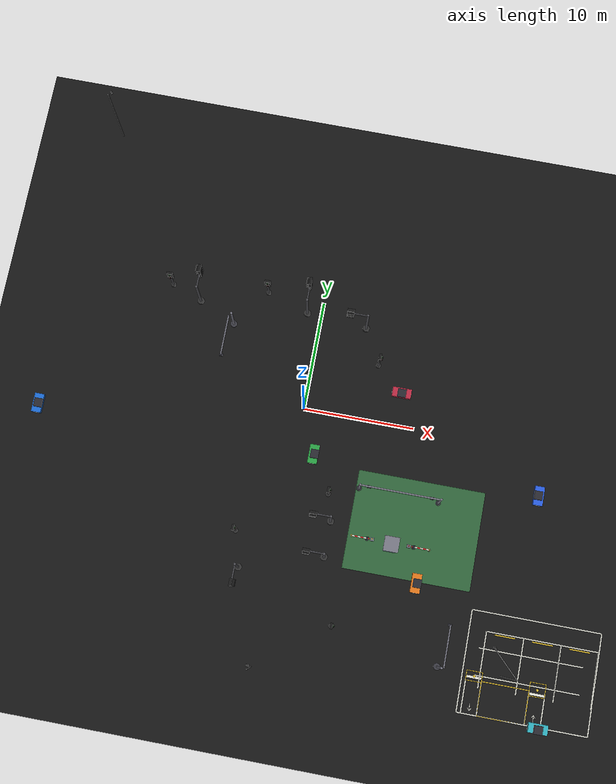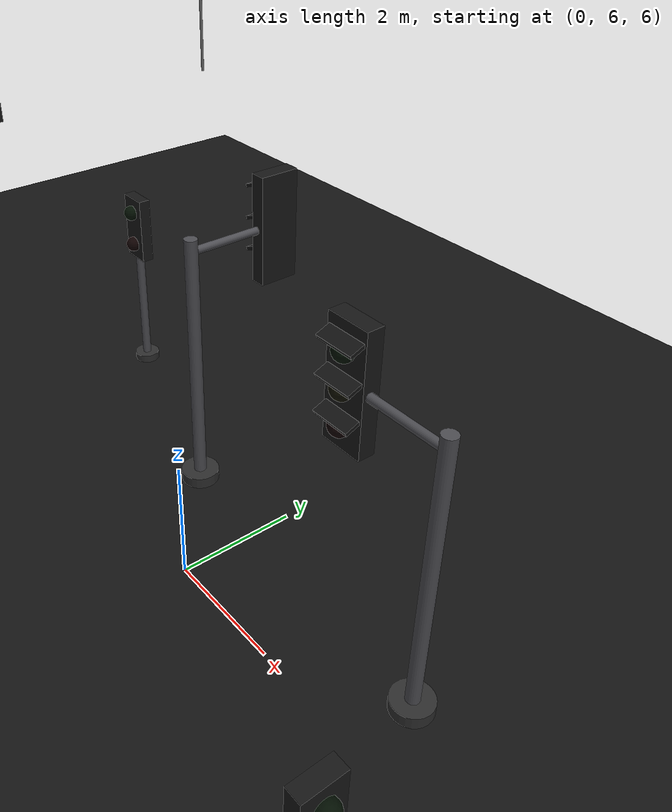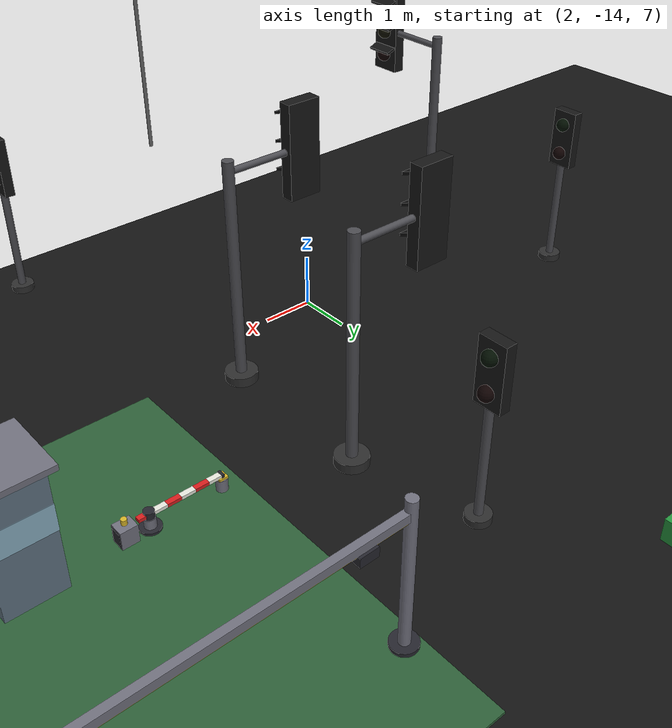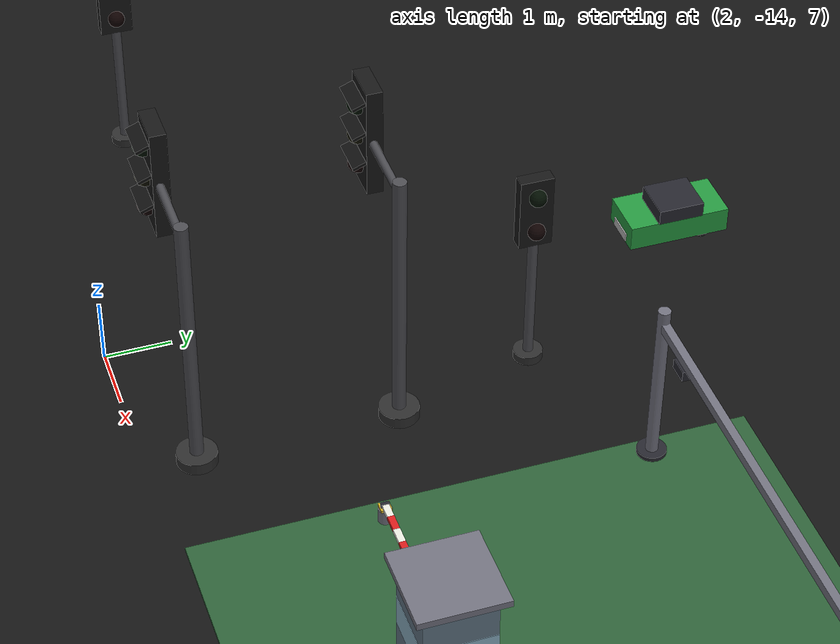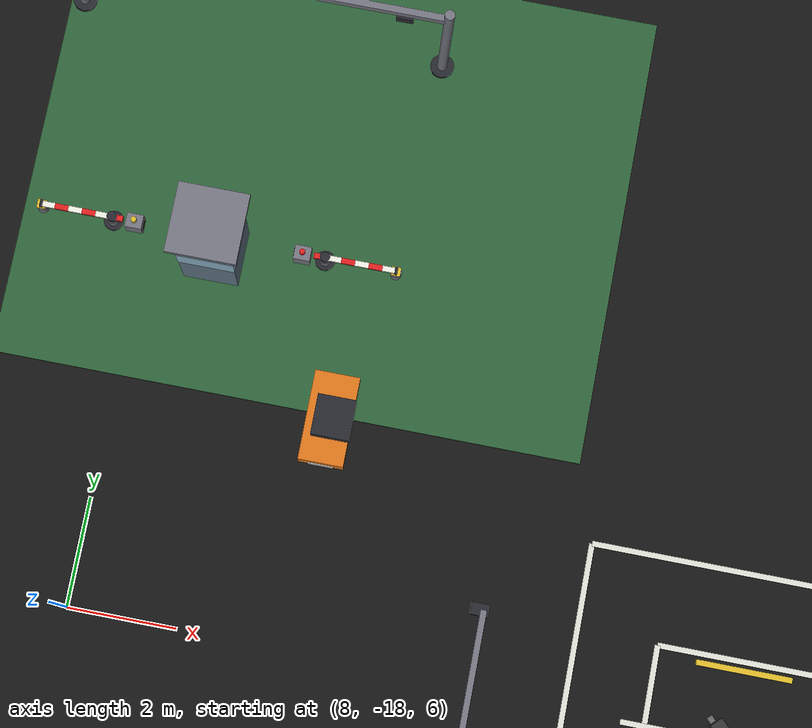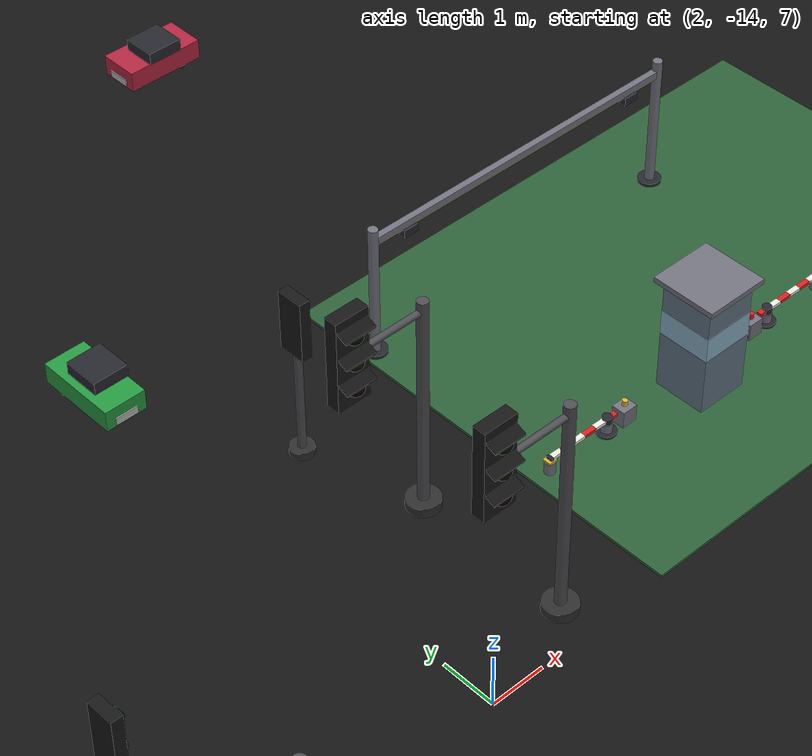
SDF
<sdf version="1.6">
 <world name="v2x_city_scene">
  <physics type="ode">
   <real_time_update_rate>1000.0</real_time_update_rate>
   <max_step>0.001</max_step>
   <real_time_factor>1</real_time_factor>
   <ode>
    <solver>
     <type>quick</type>
     <iters>150</iters>
     <precon_iters>0</precon_iters>
     <sor>1.400000</sor>
     <use_dynamic_moi_rescaling>1</use_dynamic_moi_rescaling>
    </solver>
    <constraints>
     <cfm>0.00001</cfm>
     <erp>0.2</erp>
     <contact_max_correcting_vel>2000.0</contact_max_correcting_vel>
     <contact_surface_layer>0.01000</contact_surface_layer>
    </constraints>
   </ode>
  </physics>
  <scene><ambient>0.6 0.6 0.6 1</ambient><background>0.7 0.7 0.7 1</background><shadows>true</shadows></scene>
  <light name="sun" type="directional">
   <pose>0 0 10 0 0 0</pose>
   <diffuse>0.8 0.8 0.8 1</diffuse>
   <specular>0.2 0.2 0.2 1</specular>
   <attenuation>
    <range>1000</range>
    <constant>0.9</constant>
    <linear>0.01</linear>
    <quadratic>0.001</quadratic>
   </attenuation>
   <direction>-0.5 0.1 -0.9</direction>
  </light>
  <model name="ground_plane">
   <static>true</static>
   <link name="link">
    <collision name="collision">
     <geometry><plane><normal>0 0 1</normal><size>200 200</size></plane></geometry>
    </collision>
    <visual name="visual">
     <geometry><plane><normal>0 0 1</normal><size>200 200</size></plane></geometry>
     <material>
      <ambient>0.05 0.05 0.05 1</ambient>
      <diffuse>0.08 0.08 0.08 1</diffuse>
      <specular>0.0 0.0 0.0 1</specular>
     </material>
    </visual>
   </link>
  </model>
  <model name="bldg_school">
   <static>true</static>
   <pose>-8.62 -8.88 9.2 0 0 0</pose>
   <link name="link">
    <collision name="c"><geometry><box><size>10.85 8.35 5</size></box></geometry></collision>
   </link>
  </model>
  <model name="bldg_nw">
   <static>true</static>
   <pose>-13.5 12.5 9.7 0 0 0</pose>
   <link name="link"><collision name="c"><geometry><box><size>9 9 6</size></box></geometry></collision></link>
  </model>
  <model name="bldg_tower_w">
   <static>true</static>
   <pose>-4 14 10.7 0 0 0</pose>
   <link name="link"><collision name="c"><geometry><box><size>7 7 8</size></box></geometry></collision></link>
  </model>
  <model name="bldg_tower_e">
   <static>true</static>
   <pose>9 14 10.7 0 0 0</pose>
   <link name="link"><collision name="c"><geometry><box><size>7 7 8</size></box></geometry></collision></link>
  </model>
  <model name="bldg_ne">
   <static>true</static>
   <pose>17 13.2 9.7 0 0 0</pose>
   <link name="link"><collision name="c"><geometry><box><size>9 9 6</size></box></geometry></collision></link>
  </model>
  <model name="car_1">
   <pose>-21.8 -5.0 7.0 0 0 1.5708</pose>
   <link name="chassis">
    <inertial>
     <mass>80.0</mass>
     <inertia><ixx>2.13</ixx><ixy>0</ixy><iyy>17.07</iyy><ixz>0</ixz><iyz>0</iyz><izz>17.07</izz></inertia>
    </inertial>
    <collision name="chassis_collision">
     <pose>0 0 0.25 0 0 0</pose>
     <geometry><box><size>1.6 0.8 0.4</size></box></geometry>
    </collision>
    <visual name="chassis_body">
     <pose>0 0 0.25 0 0 0</pose>
     <geometry><box><size>1.6 0.8 0.4</size></box></geometry>
     <material><ambient>0.1 0.4 0.8 1</ambient><diffuse>0.1 0.4 0.8 1</diffuse></material>
    </visual>
    <visual name="plate_rear">
     <pose>-0.81 0 0.15 0 0 3.14159265358979</pose>
     <geometry><box><size>0.02 0.44 0.14</size></box></geometry>
     <material>
      <script>
       <uri>file:///tmp/v2x_plates/placeholder/placeholder.material</uri>
       <name>v2x/plate_placeholder</name>
      </script>
     </material>
    </visual>
    <visual name="plate_front">
     <pose>0.81 0 0.15 0 0 0</pose>
     <geometry><box><size>0.02 0.44 0.14</size></box></geometry>
     <material>
      <script>
       <uri>file:///tmp/v2x_plates/placeholder/placeholder.material</uri>
       <name>v2x/plate_placeholder</name>
      </script>
     </material>
    </visual>
    <visual name="cabin">
     <pose>0 -0.08 0.57 0 0 0</pose>
     <geometry><box><size>0.72 0.68 0.24</size></box></geometry>
     <material><ambient>0.1 0.1 0.12 1</ambient><diffuse>0.15 0.15 0.18 1</diffuse></material>
    </visual>
    <sensor name="camera" type="camera">
     <pose>0.6 0 0.75 0 0.15 0</pose>
     <always_on>true</always_on>
     <update_rate>5</update_rate>
     <visualize>true</visualize>
     <camera name="front_camera">
      <horizontal_fov>1.2</horizontal_fov>
      <image><width>640</width><height>480</height><format>R8G8B8</format></image>
      <clip><near>0.05</near><far>100</far></clip>
     </camera>
     <plugin name="gazebo_ros_camera" filename="libgazebo_ros_camera.so">
      <ros>
       <namespace>/car_1</namespace>
       <remapping>~/image_raw:=camera/image_raw</remapping>
       <remapping>~/camera_info:=camera/camera_info</remapping>
      </ros>
      <camera_name>camera</camera_name>
      <frame_name>car_1/camera_link</frame_name>
     </plugin>
    </sensor>
    <sensor name="lidar" type="ray">
     <pose>0.16 0 0.55 0 0 0</pose>
     <always_on>true</always_on>
     <update_rate>10</update_rate>
     <visualize>true</visualize>
     <ray>
      <scan>
       <horizontal>
        <samples>360</samples>
        <resolution>1</resolution>
        <min_angle>-3.14159</min_angle>
        <max_angle>3.14159</max_angle>
       </horizontal>
      </scan>
      <range><min>0.12</min><max>30.0</max><resolution>0.01</resolution></range>
      <noise><type>gaussian</type><mean>0.0</mean><stddev>0.01</stddev></noise>
     </ray>
     <plugin name="gazebo_ros_ray_sensor" filename="libgazebo_ros_ray_sensor.so">
      <ros><namespace>/car_1</namespace><remapping>~/out:=scan</remapping></ros>
      <output_type>sensor_msgs/LaserScan</output_type>
      <frame_name>car_1/lidar_link</frame_name>
     </plugin>
    </sensor>
    <sensor name="imu_sensor" type="imu">
     <pose>0 0 0.20 0 0 0</pose>
     <always_on>true</always_on>
     <update_rate>200</update_rate>
     <plugin name="gazebo_ros_imu_sensor" filename="libgazebo_ros_imu_sensor.so">
      <ros><namespace>/car_1</namespace><remapping>~/out:=imu/data</remapping></ros>
      <frame_name>car_1/imu_link</frame_name>
      <initial_orientation_as_reference>false</initial_orientation_as_reference>
     </plugin>
    </sensor>
   </link>
   <link name="left_wheel_link">
    <pose>0.40 0.35 0.10 0 0 0</pose>
    <inertial>
     <mass>2.0</mass>
     <inertia>
      <ixx>0.005067</ixx>
      <iyy>0.010000</iyy>
      <izz>0.005067</izz>
      <ixy>0</ixy>
      <ixz>0</ixz>
      <iyz>0</iyz>
     </inertia>
    </inertial>
    <collision name="collision">
     <pose>0 0 0 1.5707963 0 0</pose>
     <geometry><cylinder><radius>0.10</radius><length>0.08</length></cylinder></geometry>
     <surface>
      <friction><ode><mu>1.0</mu><mu2>1.0</mu2></ode></friction>
      <contact><ode><min_depth>0.001</min_depth><kp>1e8</kp></ode></contact>
     </surface>
    </collision>
    <visual name="visual">
     <pose>0 0 0 1.5707963 0 0</pose>
     <geometry><cylinder><radius>0.10</radius><length>0.08</length></cylinder></geometry>
     <material><ambient>0.05 0.05 0.05 1</ambient><diffuse>0.1 0.1 0.1 1</diffuse></material>
    </visual>
   </link>
   <joint name="left_wheel_joint" type="revolute">
    <parent>chassis</parent>
    <child>left_wheel_link</child>
    <axis><xyz>0 1 0</xyz><dynamics><friction>0.1</friction></dynamics></axis>
   </joint>
   <link name="right_wheel_link">
    <pose>0.40 -0.35 0.10 0 0 0</pose>
    <inertial>
     <mass>2.0</mass>
     <inertia>
      <ixx>0.005067</ixx>
      <iyy>0.010000</iyy>
      <izz>0.005067</izz>
      <ixy>0</ixy>
      <ixz>0</ixz>
      <iyz>0</iyz>
     </inertia>
    </inertial>
    <collision name="collision">
     <pose>0 0 0 1.5707963 0 0</pose>
     <geometry><cylinder><radius>0.10</radius><length>0.08</length></cylinder></geometry>
     <surface>
      <friction><ode><mu>1.0</mu><mu2>1.0</mu2></ode></friction>
      <contact><ode><min_depth>0.001</min_depth><kp>1e8</kp></ode></contact>
     </surface>
    </collision>
    <visual name="visual">
     <pose>0 0 0 1.5707963 0 0</pose>
     <geometry><cylinder><radius>0.10</radius><length>0.08</length></cylinder></geometry>
     <material><ambient>0.05 0.05 0.05 1</ambient><diffuse>0.1 0.1 0.1 1</diffuse></material>
    </visual>
   </link>
   <joint name="right_wheel_joint" type="revolute">
    <parent>chassis</parent>
    <child>right_wheel_link</child>
    <axis><xyz>0 1 0</xyz><dynamics><friction>0.1</friction></dynamics></axis>
   </joint>
   <link name="caster_link">
    <pose>-0.40 0 0.06 0 0 0</pose>
    <inertial>
     <mass>0.5</mass>
     <inertia><ixx>0.001</ixx><iyy>0.001</iyy><izz>0.001</izz><ixy>0</ixy><ixz>0</ixz><iyz>0</iyz></inertia>
    </inertial>
    <collision name="collision">
     <geometry><sphere><radius>0.06</radius></sphere></geometry>
     <surface>
      <friction><ode><mu>0.0</mu><mu2>0.0</mu2></ode></friction>
      <contact><ode><min_depth>0.001</min_depth><kp>1e8</kp></ode></contact>
     </surface>
    </collision>
    <visual name="visual">
     <geometry><sphere><radius>0.06</radius></sphere></geometry>
     <material><ambient>0.2 0.2 0.2 1</ambient><diffuse>0.3 0.3 0.3 1</diffuse></material>
    </visual>
   </link>
   <joint name="caster_joint" type="fixed"><parent>chassis</parent><child>caster_link</child></joint>
   <plugin name="diff_drive" filename="libgazebo_ros_diff_drive.so">
    <ros>
     <namespace>/car_1</namespace>
     <remapping>cmd_vel:=cmd_vel</remapping>
     <remapping>odom:=odom</remapping>
    </ros>
    <update_rate>100</update_rate>
    <cmd_vel_timeout>0.3</cmd_vel_timeout>
    <left_joint>left_wheel_joint</left_joint>
    <right_joint>right_wheel_joint</right_joint>
    <wheel_separation>0.70</wheel_separation>
    <wheel_diameter>0.20</wheel_diameter>
    <max_wheel_torque>12.0</max_wheel_torque>
    <max_wheel_acceleration>6.0</max_wheel_acceleration>
    <publish_odom>true</publish_odom>
    <publish_odom_tf>true</publish_odom_tf>
    <publish_wheel_tf>true</publish_wheel_tf>
    <odometry_frame>car_1_odom</odometry_frame>
    <robot_base_frame>car_1/base_link</robot_base_frame>
   </plugin>
   <plugin name="v2x_fault_sim" filename="libv2x_fault_sim.so">
    <ros><namespace>/car_1</namespace></ros>
    <enabled>false</enabled>
    <fault_type>NONE</fault_type>
    <drift_rate>0.01</drift_rate>
    <lag_seconds>0.5</lag_seconds>
    <sensor_drop_rate>0.3</sensor_drop_rate>
   </plugin>
  </model>
  <model name="car_2">
   <pose>1.8000 -5.0000 7.0000 0 0 1.5708</pose>
   <link name="chassis">
    <inertial>
     <mass>80.0</mass>
     <inertia><ixx>2.13</ixx><ixy>0</ixy><iyy>17.07</iyy><ixz>0</ixz><iyz>0</iyz><izz>17.07</izz></inertia>
    </inertial>
    <collision name="chassis_collision">
     <pose>0 0 0.25 0 0 0</pose>
     <geometry><box><size>1.6 0.8 0.4</size></box></geometry>
    </collision>
    <visual name="chassis_body">
     <pose>0 0 0.25 0 0 0</pose>
     <geometry><box><size>1.6 0.8 0.4</size></box></geometry>
     <material><ambient>0.15 0.6 0.25 1</ambient><diffuse>0.15 0.6 0.25 1</diffuse></material>
    </visual>
    <visual name="plate_rear">
     <pose>-0.81 0 0.15 0 0 3.14159265358979</pose>
     <geometry><box><size>0.02 0.44 0.14</size></box></geometry>
     <material>
      <script>
       <uri>file:///tmp/v2x_plates/placeholder/placeholder.material</uri>
       <name>v2x/plate_placeholder</name>
      </script>
     </material>
    </visual>
    <visual name="plate_front">
     <pose>0.81 0 0.15 0 0 0</pose>
     <geometry><box><size>0.02 0.44 0.14</size></box></geometry>
     <material>
      <script>
       <uri>file:///tmp/v2x_plates/placeholder/placeholder.material</uri>
       <name>v2x/plate_placeholder</name>
      </script>
     </material>
    </visual>
    <visual name="cabin">
     <pose>0 -0.08 0.57 0 0 0</pose>
     <geometry><box><size>0.72 0.68 0.24</size></box></geometry>
     <material><ambient>0.1 0.1 0.12 1</ambient><diffuse>0.15 0.15 0.18 1</diffuse></material>
    </visual>
   </link>
   <link name="left_wheel_link">
    <pose>0.40 0.35 0.10 0 0 0</pose>
    <inertial>
     <mass>2.0</mass>
     <inertia>
      <ixx>0.005067</ixx>
      <iyy>0.010000</iyy>
      <izz>0.005067</izz>
      <ixy>0</ixy>
      <ixz>0</ixz>
      <iyz>0</iyz>
     </inertia>
    </inertial>
    <collision name="collision">
     <pose>0 0 0 1.5707963 0 0</pose>
     <geometry><cylinder><radius>0.10</radius><length>0.08</length></cylinder></geometry>
     <surface>
      <friction><ode><mu>1.0</mu><mu2>1.0</mu2></ode></friction>
      <contact><ode><min_depth>0.001</min_depth><kp>1e8</kp></ode></contact>
     </surface>
    </collision>
    <visual name="visual">
     <pose>0 0 0 1.5707963 0 0</pose>
     <geometry><cylinder><radius>0.10</radius><length>0.08</length></cylinder></geometry>
     <material><ambient>0.05 0.05 0.05 1</ambient><diffuse>0.1 0.1 0.1 1</diffuse></material>
    </visual>
   </link>
   <joint name="left_wheel_joint" type="revolute">
    <parent>chassis</parent>
    <child>left_wheel_link</child>
    <axis><xyz>0 1 0</xyz><dynamics><friction>0.1</friction></dynamics></axis>
   </joint>
   <link name="right_wheel_link">
    <pose>0.40 -0.35 0.10 0 0 0</pose>
    <inertial>
     <mass>2.0</mass>
     <inertia>
      <ixx>0.005067</ixx>
      <iyy>0.010000</iyy>
      <izz>0.005067</izz>
      <ixy>0</ixy>
      <ixz>0</ixz>
      <iyz>0</iyz>
     </inertia>
    </inertial>
    <collision name="collision">
     <pose>0 0 0 1.5707963 0 0</pose>
     <geometry><cylinder><radius>0.10</radius><length>0.08</length></cylinder></geometry>
     <surface>
      <friction><ode><mu>1.0</mu><mu2>1.0</mu2></ode></friction>
      <contact><ode><min_depth>0.001</min_depth><kp>1e8</kp></ode></contact>
     </surface>
    </collision>
    <visual name="visual">
     <pose>0 0 0 1.5707963 0 0</pose>
     <geometry><cylinder><radius>0.10</radius><length>0.08</length></cylinder></geometry>
     <material><ambient>0.05 0.05 0.05 1</ambient><diffuse>0.1 0.1 0.1 1</diffuse></material>
    </visual>
   </link>
   <joint name="right_wheel_joint" type="revolute">
    <parent>chassis</parent>
    <child>right_wheel_link</child>
    <axis><xyz>0 1 0</xyz><dynamics><friction>0.1</friction></dynamics></axis>
   </joint>
   <link name="caster_link">
    <pose>-0.40 0 0.06 0 0 0</pose>
    <inertial>
     <mass>0.5</mass>
     <inertia><ixx>0.001</ixx><iyy>0.001</iyy><izz>0.001</izz><ixy>0</ixy><ixz>0</ixz><iyz>0</iyz></inertia>
    </inertial>
    <collision name="collision">
     <geometry><sphere><radius>0.06</radius></sphere></geometry>
     <surface>
      <friction><ode><mu>0.0</mu><mu2>0.0</mu2></ode></friction>
      <contact><ode><min_depth>0.001</min_depth><kp>1e8</kp></ode></contact>
     </surface>
    </collision>
    <visual name="visual">
     <geometry><sphere><radius>0.06</radius></sphere></geometry>
     <material><ambient>0.2 0.2 0.2 1</ambient><diffuse>0.3 0.3 0.3 1</diffuse></material>
    </visual>
   </link>
   <joint name="caster_joint" type="fixed"><parent>chassis</parent><child>caster_link</child></joint>
   <plugin name="diff_drive" filename="libgazebo_ros_diff_drive.so">
    <ros>
     <namespace>/car_2</namespace>
     <remapping>cmd_vel:=cmd_vel</remapping>
     <remapping>odom:=odom</remapping>
    </ros>
    <update_rate>100</update_rate>
    <cmd_vel_timeout>0.3</cmd_vel_timeout>
    <left_joint>left_wheel_joint</left_joint>
    <right_joint>right_wheel_joint</right_joint>
    <wheel_separation>0.70</wheel_separation>
    <wheel_diameter>0.20</wheel_diameter>
    <max_wheel_torque>12.0</max_wheel_torque>
    <max_wheel_acceleration>6.0</max_wheel_acceleration>
    <publish_odom>true</publish_odom>
    <publish_odom_tf>false</publish_odom_tf>
    <publish_wheel_tf>false</publish_wheel_tf>
    <odometry_frame>car_2_odom</odometry_frame>
    <robot_base_frame>car_2/base_link</robot_base_frame>
   </plugin>
  </model>
  <model name="car_3">
   <pose>12.0000 -13.9500 7.0000 0 0 1.5708</pose>
   <link name="chassis">
    <inertial>
     <mass>80.0</mass>
     <inertia><ixx>2.13</ixx><ixy>0</ixy><iyy>17.07</iyy><ixz>0</ixz><iyz>0</iyz><izz>17.07</izz></inertia>
    </inertial>
    <collision name="chassis_collision">
     <pose>0 0 0.25 0 0 0</pose>
     <geometry><box><size>1.6 0.8 0.4</size></box></geometry>
    </collision>
    <visual name="chassis_body">
     <pose>0 0 0.25 0 0 0</pose>
     <geometry><box><size>1.6 0.8 0.4</size></box></geometry>
     <material><ambient>0.85 0.45 0.10 1</ambient><diffuse>0.85 0.45 0.10 1</diffuse></material>
    </visual>
    <visual name="plate_rear">
     <pose>-0.81 0 0.15 0 0 3.14159265358979</pose>
     <geometry><box><size>0.02 0.44 0.14</size></box></geometry>
     <material>
      <script>
       <uri>file:///tmp/v2x_plates/placeholder/placeholder.material</uri>
       <name>v2x/plate_placeholder</name>
      </script>
     </material>
    </visual>
    <visual name="plate_front">
     <pose>0.81 0 0.15 0 0 0</pose>
     <geometry><box><size>0.02 0.44 0.14</size></box></geometry>
     <material>
      <script>
       <uri>file:///tmp/v2x_plates/placeholder/placeholder.material</uri>
       <name>v2x/plate_placeholder</name>
      </script>
     </material>
    </visual>
    <visual name="cabin">
     <pose>0 -0.08 0.57 0 0 0</pose>
     <geometry><box><size>0.72 0.68 0.24</size></box></geometry>
     <material><ambient>0.1 0.1 0.12 1</ambient><diffuse>0.15 0.15 0.18 1</diffuse></material>
    </visual>
   </link>
   <link name="left_wheel_link">
    <pose>0.40 0.35 0.10 0 0 0</pose>
    <inertial>
     <mass>2.0</mass>
     <inertia>
      <ixx>0.005067</ixx>
      <iyy>0.010000</iyy>
      <izz>0.005067</izz>
      <ixy>0</ixy>
      <ixz>0</ixz>
      <iyz>0</iyz>
     </inertia>
    </inertial>
    <collision name="collision">
     <pose>0 0 0 1.5707963 0 0</pose>
     <geometry><cylinder><radius>0.10</radius><length>0.08</length></cylinder></geometry>
     <surface>
      <friction><ode><mu>1.0</mu><mu2>1.0</mu2></ode></friction>
      <contact><ode><min_depth>0.001</min_depth><kp>1e8</kp></ode></contact>
     </surface>
    </collision>
    <visual name="visual">
     <pose>0 0 0 1.5707963 0 0</pose>
     <geometry><cylinder><radius>0.10</radius><length>0.08</length></cylinder></geometry>
     <material><ambient>0.05 0.05 0.05 1</ambient><diffuse>0.1 0.1 0.1 1</diffuse></material>
    </visual>
   </link>
   <joint name="left_wheel_joint" type="revolute">
    <parent>chassis</parent>
    <child>left_wheel_link</child>
    <axis><xyz>0 1 0</xyz><dynamics><friction>0.1</friction></dynamics></axis>
   </joint>
   <link name="right_wheel_link">
    <pose>0.40 -0.35 0.10 0 0 0</pose>
    <inertial>
     <mass>2.0</mass>
     <inertia>
      <ixx>0.005067</ixx>
      <iyy>0.010000</iyy>
      <izz>0.005067</izz>
      <ixy>0</ixy>
      <ixz>0</ixz>
      <iyz>0</iyz>
     </inertia>
    </inertial>
    <collision name="collision">
     <pose>0 0 0 1.5707963 0 0</pose>
     <geometry><cylinder><radius>0.10</radius><length>0.08</length></cylinder></geometry>
     <surface>
      <friction><ode><mu>1.0</mu><mu2>1.0</mu2></ode></friction>
      <contact><ode><min_depth>0.001</min_depth><kp>1e8</kp></ode></contact>
     </surface>
    </collision>
    <visual name="visual">
     <pose>0 0 0 1.5707963 0 0</pose>
     <geometry><cylinder><radius>0.10</radius><length>0.08</length></cylinder></geometry>
     <material><ambient>0.05 0.05 0.05 1</ambient><diffuse>0.1 0.1 0.1 1</diffuse></material>
    </visual>
   </link>
   <joint name="right_wheel_joint" type="revolute">
    <parent>chassis</parent>
    <child>right_wheel_link</child>
    <axis><xyz>0 1 0</xyz><dynamics><friction>0.1</friction></dynamics></axis>
   </joint>
   <link name="caster_link">
    <pose>-0.40 0 0.06 0 0 0</pose>
    <inertial>
     <mass>0.5</mass>
     <inertia><ixx>0.001</ixx><iyy>0.001</iyy><izz>0.001</izz><ixy>0</ixy><ixz>0</ixz><iyz>0</iyz></inertia>
    </inertial>
    <collision name="collision">
     <geometry><sphere><radius>0.06</radius></sphere></geometry>
     <surface>
      <friction><ode><mu>0.0</mu><mu2>0.0</mu2></ode></friction>
      <contact><ode><min_depth>0.001</min_depth><kp>1e8</kp></ode></contact>
     </surface>
    </collision>
    <visual name="visual">
     <geometry><sphere><radius>0.06</radius></sphere></geometry>
     <material><ambient>0.2 0.2 0.2 1</ambient><diffuse>0.3 0.3 0.3 1</diffuse></material>
    </visual>
   </link>
   <joint name="caster_joint" type="fixed"><parent>chassis</parent><child>caster_link</child></joint>
   <plugin name="diff_drive" filename="libgazebo_ros_diff_drive.so">
    <ros>
     <namespace>/car_3</namespace>
     <remapping>cmd_vel:=cmd_vel</remapping>
     <remapping>odom:=odom</remapping>
    </ros>
    <update_rate>100</update_rate>
    <cmd_vel_timeout>0.3</cmd_vel_timeout>
    <left_joint>left_wheel_joint</left_joint>
    <right_joint>right_wheel_joint</right_joint>
    <wheel_separation>0.70</wheel_separation>
    <wheel_diameter>0.20</wheel_diameter>
    <max_wheel_torque>12.0</max_wheel_torque>
    <max_wheel_acceleration>6.0</max_wheel_acceleration>
    <publish_odom>true</publish_odom>
    <publish_odom_tf>false</publish_odom_tf>
    <publish_wheel_tf>false</publish_wheel_tf>
    <odometry_frame>car_3_odom</odometry_frame>
    <robot_base_frame>car_3/base_link</robot_base_frame>
   </plugin>
  </model>
  <model name="car_4">
   <pose>20.8 -5.0 7.0 0 0 -1.5708</pose>
   <link name="chassis">
    <inertial>
     <mass>80.0</mass>
     <inertia><ixx>2.13</ixx><ixy>0</ixy><iyy>17.07</iyy><ixz>0</ixz><iyz>0</iyz><izz>17.07</izz></inertia>
    </inertial>
    <collision name="chassis_collision">
     <pose>0 0 0.25 0 0 0</pose>
     <geometry><box><size>1.6 0.8 0.4</size></box></geometry>
    </collision>
    <visual name="chassis_body">
     <pose>0 0 0.25 0 0 0</pose>
     <geometry><box><size>1.6 0.8 0.4</size></box></geometry>
     <material><ambient>0.15 0.35 0.85 1</ambient><diffuse>0.15 0.35 0.85 1</diffuse></material>
    </visual>
    <visual name="plate_rear">
     <pose>-0.81 0 0.15 0 0 3.14159265358979</pose>
     <geometry><box><size>0.02 0.44 0.14</size></box></geometry>
     <material>
      <script>
       <uri>file:///tmp/v2x_plates/placeholder/placeholder.material</uri>
       <name>v2x/plate_placeholder</name>
      </script>
     </material>
    </visual>
    <visual name="plate_front">
     <pose>0.81 0 0.15 0 0 0</pose>
     <geometry><box><size>0.02 0.44 0.14</size></box></geometry>
     <material>
      <script>
       <uri>file:///tmp/v2x_plates/placeholder/placeholder.material</uri>
       <name>v2x/plate_placeholder</name>
      </script>
     </material>
    </visual>
    <visual name="cabin">
     <pose>0 -0.08 0.57 0 0 0</pose>
     <geometry><box><size>0.72 0.68 0.24</size></box></geometry>
     <material><ambient>0.1 0.1 0.12 1</ambient><diffuse>0.15 0.15 0.18 1</diffuse></material>
    </visual>
   </link>
   <link name="left_wheel_link">
    <pose>0.40 0.35 0.10 0 0 0</pose>
    <inertial>
     <mass>2.0</mass>
     <inertia>
      <ixx>0.005067</ixx>
      <iyy>0.010000</iyy>
      <izz>0.005067</izz>
      <ixy>0</ixy>
      <ixz>0</ixz>
      <iyz>0</iyz>
     </inertia>
    </inertial>
    <collision name="collision">
     <pose>0 0 0 1.5707963 0 0</pose>
     <geometry><cylinder><radius>0.10</radius><length>0.08</length></cylinder></geometry>
     <surface>
      <friction><ode><mu>1.0</mu><mu2>1.0</mu2></ode></friction>
      <contact><ode><min_depth>0.001</min_depth><kp>1e8</kp></ode></contact>
     </surface>
    </collision>
    <visual name="visual">
     <pose>0 0 0 1.5707963 0 0</pose>
     <geometry><cylinder><radius>0.10</radius><length>0.08</length></cylinder></geometry>
     <material><ambient>0.05 0.05 0.05 1</ambient><diffuse>0.1 0.1 0.1 1</diffuse></material>
    </visual>
   </link>
   <joint name="left_wheel_joint" type="revolute">
    <parent>chassis</parent>
    <child>left_wheel_link</child>
    <axis><xyz>0 1 0</xyz><dynamics><friction>0.1</friction></dynamics></axis>
   </joint>
   <link name="right_wheel_link">
    <pose>0.40 -0.35 0.10 0 0 0</pose>
    <inertial>
     <mass>2.0</mass>
     <inertia>
      <ixx>0.005067</ixx>
      <iyy>0.010000</iyy>
      <izz>0.005067</izz>
      <ixy>0</ixy>
      <ixz>0</ixz>
      <iyz>0</iyz>
     </inertia>
    </inertial>
    <collision name="collision">
     <pose>0 0 0 1.5707963 0 0</pose>
     <geometry><cylinder><radius>0.10</radius><length>0.08</length></cylinder></geometry>
     <surface>
      <friction><ode><mu>1.0</mu><mu2>1.0</mu2></ode></friction>
      <contact><ode><min_depth>0.001</min_depth><kp>1e8</kp></ode></contact>
     </surface>
    </collision>
    <visual name="visual">
     <pose>0 0 0 1.5707963 0 0</pose>
     <geometry><cylinder><radius>0.10</radius><length>0.08</length></cylinder></geometry>
     <material><ambient>0.05 0.05 0.05 1</ambient><diffuse>0.1 0.1 0.1 1</diffuse></material>
    </visual>
   </link>
   <joint name="right_wheel_joint" type="revolute">
    <parent>chassis</parent>
    <child>right_wheel_link</child>
    <axis><xyz>0 1 0</xyz><dynamics><friction>0.1</friction></dynamics></axis>
   </joint>
   <link name="caster_link">
    <pose>-0.40 0 0.06 0 0 0</pose>
    <inertial>
     <mass>0.5</mass>
     <inertia><ixx>0.001</ixx><iyy>0.001</iyy><izz>0.001</izz><ixy>0</ixy><ixz>0</ixz><iyz>0</iyz></inertia>
    </inertial>
    <collision name="collision">
     <geometry><sphere><radius>0.06</radius></sphere></geometry>
     <surface>
      <friction><ode><mu>0.0</mu><mu2>0.0</mu2></ode></friction>
      <contact><ode><min_depth>0.001</min_depth><kp>1e8</kp></ode></contact>
     </surface>
    </collision>
    <visual name="visual">
     <geometry><sphere><radius>0.06</radius></sphere></geometry>
     <material><ambient>0.2 0.2 0.2 1</ambient><diffuse>0.3 0.3 0.3 1</diffuse></material>
    </visual>
   </link>
   <joint name="caster_joint" type="fixed"><parent>chassis</parent><child>caster_link</child></joint>
   <plugin name="diff_drive" filename="libgazebo_ros_diff_drive.so">
    <ros>
     <namespace>/car_4</namespace>
     <remapping>cmd_vel:=cmd_vel</remapping>
     <remapping>odom:=odom</remapping>
    </ros>
    <update_rate>100</update_rate>
    <cmd_vel_timeout>0.3</cmd_vel_timeout>
    <left_joint>left_wheel_joint</left_joint>
    <right_joint>right_wheel_joint</right_joint>
    <wheel_separation>0.70</wheel_separation>
    <wheel_diameter>0.20</wheel_diameter>
    <max_wheel_torque>12.0</max_wheel_torque>
    <max_wheel_acceleration>6.0</max_wheel_acceleration>
    <publish_odom>true</publish_odom>
    <publish_odom_tf>false</publish_odom_tf>
    <publish_wheel_tf>false</publish_wheel_tf>
    <odometry_frame>car_4_odom</odometry_frame>
    <robot_base_frame>car_4/base_link</robot_base_frame>
   </plugin>
  </model>
  <model name="car_5">
   <pose>8.15 1.5 7.0 0 0 0.0</pose>
   <link name="chassis">
    <inertial>
     <mass>80.0</mass>
     <inertia><ixx>2.13</ixx><ixy>0</ixy><iyy>17.07</iyy><ixz>0</ixz><iyz>0</iyz><izz>17.07</izz></inertia>
    </inertial>
    <collision name="chassis_collision">
     <pose>0 0 0.25 0 0 0</pose>
     <geometry><box><size>1.6 0.8 0.4</size></box></geometry>
    </collision>
    <visual name="chassis_body">
     <pose>0 0 0.25 0 0 0</pose>
     <geometry><box><size>1.6 0.8 0.4</size></box></geometry>
     <material><ambient>0.70 0.15 0.25 1</ambient><diffuse>0.70 0.15 0.25 1</diffuse></material>
    </visual>
    <visual name="plate_rear">
     <pose>-0.81 0 0.15 0 0 3.14159265358979</pose>
     <geometry><box><size>0.02 0.44 0.14</size></box></geometry>
     <material>
      <script>
       <uri>file:///tmp/v2x_plates/placeholder/placeholder.material</uri>
       <name>v2x/plate_placeholder</name>
      </script>
     </material>
    </visual>
    <visual name="plate_front">
     <pose>0.81 0 0.15 0 0 0</pose>
     <geometry><box><size>0.02 0.44 0.14</size></box></geometry>
     <material>
      <script>
       <uri>file:///tmp/v2x_plates/placeholder/placeholder.material</uri>
       <name>v2x/plate_placeholder</name>
      </script>
     </material>
    </visual>
    <visual name="cabin">
     <pose>0 -0.08 0.57 0 0 0</pose>
     <geometry><box><size>0.72 0.68 0.24</size></box></geometry>
     <material><ambient>0.1 0.1 0.12 1</ambient><diffuse>0.15 0.15 0.18 1</diffuse></material>
    </visual>
   </link>
   <link name="left_wheel_link">
    <pose>0.40 0.35 0.10 0 0 0</pose>
    <inertial>
     <mass>2.0</mass>
     <inertia>
      <ixx>0.005067</ixx>
      <iyy>0.010000</iyy>
      <izz>0.005067</izz>
      <ixy>0</ixy>
      <ixz>0</ixz>
      <iyz>0</iyz>
     </inertia>
    </inertial>
    <collision name="collision">
     <pose>0 0 0 1.5707963 0 0</pose>
     <geometry><cylinder><radius>0.10</radius><length>0.08</length></cylinder></geometry>
     <surface>
      <friction><ode><mu>1.0</mu><mu2>1.0</mu2></ode></friction>
      <contact><ode><min_depth>0.001</min_depth><kp>1e8</kp></ode></contact>
     </surface>
    </collision>
    <visual name="visual">
     <pose>0 0 0 1.5707963 0 0</pose>
     <geometry><cylinder><radius>0.10</radius><length>0.08</length></cylinder></geometry>
     <material><ambient>0.05 0.05 0.05 1</ambient><diffuse>0.1 0.1 0.1 1</diffuse></material>
    </visual>
   </link>
   <joint name="left_wheel_joint" type="revolute">
    <parent>chassis</parent>
    <child>left_wheel_link</child>
    <axis><xyz>0 1 0</xyz><dynamics><friction>0.1</friction></dynamics></axis>
   </joint>
   <link name="right_wheel_link">
    <pose>0.40 -0.35 0.10 0 0 0</pose>
    <inertial>
     <mass>2.0</mass>
     <inertia>
      <ixx>0.005067</ixx>
      <iyy>0.010000</iyy>
      <izz>0.005067</izz>
      <ixy>0</ixy>
      <ixz>0</ixz>
      <iyz>0</iyz>
     </inertia>
    </inertial>
    <collision name="collision">
     <pose>0 0 0 1.5707963 0 0</pose>
     <geometry><cylinder><radius>0.10</radius><length>0.08</length></cylinder></geometry>
     <surface>
      <friction><ode><mu>1.0</mu><mu2>1.0</mu2></ode></friction>
      <contact><ode><min_depth>0.001</min_depth><kp>1e8</kp></ode></contact>
     </surface>
    </collision>
    <visual name="visual">
     <pose>0 0 0 1.5707963 0 0</pose>
     <geometry><cylinder><radius>0.10</radius><length>0.08</length></cylinder></geometry>
     <material><ambient>0.05 0.05 0.05 1</ambient><diffuse>0.1 0.1 0.1 1</diffuse></material>
    </visual>
   </link>
   <joint name="right_wheel_joint" type="revolute">
    <parent>chassis</parent>
    <child>right_wheel_link</child>
    <axis><xyz>0 1 0</xyz><dynamics><friction>0.1</friction></dynamics></axis>
   </joint>
   <link name="caster_link">
    <pose>-0.40 0 0.06 0 0 0</pose>
    <inertial>
     <mass>0.5</mass>
     <inertia><ixx>0.001</ixx><iyy>0.001</iyy><izz>0.001</izz><ixy>0</ixy><ixz>0</ixz><iyz>0</iyz></inertia>
    </inertial>
    <collision name="collision">
     <geometry><sphere><radius>0.06</radius></sphere></geometry>
     <surface>
      <friction><ode><mu>0.0</mu><mu2>0.0</mu2></ode></friction>
      <contact><ode><min_depth>0.001</min_depth><kp>1e8</kp></ode></contact>
     </surface>
    </collision>
    <visual name="visual">
     <geometry><sphere><radius>0.06</radius></sphere></geometry>
     <material><ambient>0.2 0.2 0.2 1</ambient><diffuse>0.3 0.3 0.3 1</diffuse></material>
    </visual>
   </link>
   <joint name="caster_joint" type="fixed"><parent>chassis</parent><child>caster_link</child></joint>
   <plugin name="diff_drive" filename="libgazebo_ros_diff_drive.so">
    <ros>
     <namespace>/car_5</namespace>
     <remapping>cmd_vel:=cmd_vel</remapping>
     <remapping>odom:=odom</remapping>
    </ros>
    <update_rate>100</update_rate>
    <cmd_vel_timeout>0.3</cmd_vel_timeout>
    <left_joint>left_wheel_joint</left_joint>
    <right_joint>right_wheel_joint</right_joint>
    <wheel_separation>0.70</wheel_separation>
    <wheel_diameter>0.20</wheel_diameter>
    <max_wheel_torque>12.0</max_wheel_torque>
    <max_wheel_acceleration>6.0</max_wheel_acceleration>
    <publish_odom>true</publish_odom>
    <publish_odom_tf>false</publish_odom_tf>
    <publish_wheel_tf>false</publish_wheel_tf>
    <odometry_frame>car_5_odom</odometry_frame>
    <robot_base_frame>car_5/base_link</robot_base_frame>
   </plugin>
  </model>
  <model name="speed_cam">
   <static>true</static>
   <pose>0 -23 12.7 0 0 0</pose>
   <link name="link">
    <visual name="pole">
     <pose>0 0 -3 0 0 0</pose>
     <geometry><cylinder><radius>0.05</radius><length>6.0</length></cylinder></geometry>
     <material><ambient>0.3 0.3 0.3 1</ambient><diffuse>0.4 0.4 0.4 1</diffuse></material>
    </visual>
    <collision name="pole_collision">
     <pose>0 0 -3 0 0 0</pose>
     <geometry><cylinder><radius>0.05</radius><length>6.0</length></cylinder></geometry>
    </collision>
    <visual name="camera_box">
     <pose>0 0.3 0 0 0 0</pose>
     <geometry><box><size>0.3 0.2 0.15</size></box></geometry>
     <material><ambient>0.1 0.1 0.1 1</ambient><diffuse>0.2 0.2 0.2 1</diffuse></material>
    </visual>
    <sensor name="speed_camera_sensor" type="camera">
     <pose>0 0.3 0 0 0.5 0</pose>
     <always_on>true</always_on>
     <update_rate>5</update_rate>
     <visualize>true</visualize>
     <camera name="speed_cam">
      <horizontal_fov>1.0</horizontal_fov>
      <image><width>640</width><height>480</height><format>R8G8B8</format></image>
      <clip><near>0.05</near><far>100</far></clip>
     </camera>
     <plugin name="gazebo_ros_camera" filename="libgazebo_ros_camera.so">
      <ros>
       <namespace>/speed_cam</namespace>
       <remapping>~/image_raw:=camera/image_raw</remapping>
       <remapping>~/camera_info:=camera/camera_info</remapping>
      </ros>
      <camera_name>speed_cam</camera_name>
      <frame_name>speed_cam/camera_link</frame_name>
     </plugin>
    </sensor>
   </link>
  </model>
  <model name="intersection_cam">
   <static>true</static>
   <pose>20 -20 14.7 0 0 2.356</pose>
   <link name="link">
    <visual name="pole">
     <pose>0 0 -4 0 0 0</pose>
     <geometry><cylinder><radius>0.06</radius><length>8.0</length></cylinder></geometry>
     <material><ambient>0.3 0.3 0.3 1</ambient><diffuse>0.4 0.4 0.4 1</diffuse></material>
    </visual>
    <collision name="pole_collision">
     <pose>0 0 -4 0 0 0</pose>
     <geometry><cylinder><radius>0.06</radius><length>8.0</length></cylinder></geometry>
    </collision>
    <visual name="arm">
     <pose>1.5 0 0 0 0 0</pose>
     <geometry><box><size>3.0 0.08 0.08</size></box></geometry>
     <material><ambient>0.3 0.3 0.3 1</ambient><diffuse>0.4 0.4 0.4 1</diffuse></material>
    </visual>
    <visual name="camera_box">
     <pose>2.8 0 0.2 0 0 0</pose>
     <geometry><box><size>0.25 0.18 0.15</size></box></geometry>
     <material><ambient>0.1 0.1 0.1 1</ambient><diffuse>0.2 0.2 0.2 1</diffuse></material>
    </visual>
    <sensor name="intersection_camera_sensor" type="camera">
     <pose>2.8 0 0.2 0 0.45 0</pose>
     <always_on>true</always_on>
     <update_rate>5</update_rate>
     <visualize>true</visualize>
     <camera name="intersection_cam">
      <horizontal_fov>1.4</horizontal_fov>
      <image><width>800</width><height>600</height><format>R8G8B8</format></image>
      <clip><near>0.05</near><far>150</far></clip>
     </camera>
     <plugin name="gazebo_ros_camera" filename="libgazebo_ros_camera.so">
      <ros>
       <namespace>/intersection_cam</namespace>
       <remapping>~/image_raw:=camera/image_raw</remapping>
       <remapping>~/camera_info:=camera/camera_info</remapping>
      </ros>
      <camera_name>intersection_cam</camera_name>
      <frame_name>intersection_cam/camera_link</frame_name>
     </plugin>
    </sensor>
   </link>
  </model>
  <model name="monitor_cam">
   <static>true</static>
   <pose>-20 20 14.7 0 0 -0.785</pose>
   <link name="link">
    <visual name="pole">
     <pose>0 0 -4 0 0 0</pose>
     <geometry><cylinder><radius>0.05</radius><length>8.0</length></cylinder></geometry>
     <material><ambient>0.3 0.3 0.3 1</ambient><diffuse>0.4 0.4 0.4 1</diffuse></material>
    </visual>
    <collision name="pole_collision">
     <pose>0 0 -4 0 0 0</pose>
     <geometry><cylinder><radius>0.05</radius><length>8.0</length></cylinder></geometry>
    </collision>
    <visual name="camera_box">
     <pose>0 0.3 0 0 0 0</pose>
     <geometry><box><size>0.25 0.18 0.15</size></box></geometry>
     <material><ambient>0.1 0.1 0.1 1</ambient><diffuse>0.2 0.2 0.2 1</diffuse></material>
    </visual>
    <sensor name="monitor_camera_sensor" type="camera">
     <pose>0 0.3 0 0 0.5 0</pose>
     <always_on>true</always_on>
     <update_rate>5</update_rate>
     <visualize>true</visualize>
     <camera name="monitor_cam">
      <horizontal_fov>1.2</horizontal_fov>
      <image><width>640</width><height>480</height><format>R8G8B8</format></image>
      <clip><near>0.05</near><far>100</far></clip>
     </camera>
     <plugin name="gazebo_ros_camera" filename="libgazebo_ros_camera.so">
      <ros>
       <namespace>/monitor_cam</namespace>
       <remapping>~/image_raw:=camera/image_raw</remapping>
       <remapping>~/camera_info:=camera/camera_info</remapping>
      </ros>
      <camera_name>monitor_cam</camera_name>
      <frame_name>monitor_cam/camera_link</frame_name>
     </plugin>
    </sensor>
   </link>
  </model>
  <model name="tl_j1_ns">
   <static>true</static>
   <pose>4.2 -10.2 6.7 0 0 0</pose>
   <link name="pole_link">
    <visual name="base_visual">
     <pose>0 0 0.09 0 0 0</pose>
     <geometry><cylinder><radius>0.30</radius><length>0.18</length></cylinder></geometry>
     <material><ambient>0.10 0.10 0.10 1</ambient><diffuse>0.18 0.18 0.18 1</diffuse></material>
    </visual>
    <visual name="pole_visual">
     <pose>0 0 2.20 0 0 0</pose>
     <geometry><cylinder><radius>0.10</radius><length>4.10</length></cylinder></geometry>
     <material><ambient>0.16 0.16 0.16 1</ambient><diffuse>0.30 0.30 0.32 1</diffuse></material>
    </visual>
    <visual name="arm_visual">
     <pose>-0.75 0 4.05 0 1.5708 0</pose>
     <geometry><cylinder><radius>0.06</radius><length>1.60</length></cylinder></geometry>
     <material><ambient>0.16 0.16 0.16 1</ambient><diffuse>0.30 0.30 0.32 1</diffuse></material>
    </visual>
    <visual name="housing_visual">
     <pose>-1.45 0.02 4.05 0 0 0</pose>
     <geometry><box><size>0.62 0.24 1.70</size></box></geometry>
     <material><ambient>0.04 0.04 0.04 1</ambient><diffuse>0.09 0.09 0.09 1</diffuse></material>
    </visual>
    <visual name="red_visor">
     <pose>-1.45 -0.15 3.70 0.38 0 0</pose>
     <geometry><box><size>0.56 0.30 0.05</size></box></geometry>
     <material><ambient>0.03 0.03 0.03 1</ambient><diffuse>0.07 0.07 0.07 1</diffuse></material>
    </visual>
    <visual name="yellow_visor">
     <pose>-1.45 -0.15 4.20 0.38 0 0</pose>
     <geometry><box><size>0.56 0.30 0.05</size></box></geometry>
     <material><ambient>0.03 0.03 0.03 1</ambient><diffuse>0.07 0.07 0.07 1</diffuse></material>
    </visual>
    <visual name="green_visor">
     <pose>-1.45 -0.15 4.70 0.38 0 0</pose>
     <geometry><box><size>0.56 0.30 0.05</size></box></geometry>
     <material><ambient>0.03 0.03 0.03 1</ambient><diffuse>0.07 0.07 0.07 1</diffuse></material>
    </visual>
    <collision name="pole_collision">
     <pose>0 0 2.20 0 0 0</pose>
     <geometry><cylinder><radius>0.13</radius><length>4.10</length></cylinder></geometry>
    </collision>
   </link>
   <link name="red_link">
    <pose>-1.45 -0.13 3.55 0 0 0</pose>
    <visual name="red_visual">
     <geometry><sphere><radius>0.15</radius></sphere></geometry>
     <material><ambient>0.05 0 0 1</ambient><diffuse>0.05 0 0 1</diffuse><emissive>0.05 0 0 1</emissive></material>
    </visual>
   </link>
   <link name="yellow_link">
    <pose>-1.45 -0.13 4.05 0 0 0</pose>
    <visual name="yellow_visual">
     <geometry><sphere><radius>0.15</radius></sphere></geometry>
     <material>
      <ambient>0.05 0.05 0 1</ambient>
      <diffuse>0.05 0.05 0 1</diffuse>
      <emissive>0.05 0.05 0 1</emissive>
     </material>
    </visual>
   </link>
   <link name="green_link">
    <pose>-1.45 -0.13 4.55 0 0 0</pose>
    <visual name="green_visual">
     <geometry><sphere><radius>0.15</radius></sphere></geometry>
     <material><ambient>0 0.05 0 1</ambient><diffuse>0 0.05 0 1</diffuse><emissive>0 0.05 0 1</emissive></material>
    </visual>
   </link>
   <plugin name="traffic_light" filename="libtraffic_light_plugin.so">
    <topic>traffic_light/J1_ns/state</topic>
   </plugin>
  </model>
  <model name="tl_j1_ew">
   <static>true</static>
   <pose>-10.2 6.4 6.7 0 0 -1.5708</pose>
   <link name="pole_link">
    <visual name="base_visual">
     <pose>0 0 0.09 0 0 0</pose>
     <geometry><cylinder><radius>0.30</radius><length>0.18</length></cylinder></geometry>
     <material><ambient>0.10 0.10 0.10 1</ambient><diffuse>0.18 0.18 0.18 1</diffuse></material>
    </visual>
    <visual name="pole_visual">
     <pose>0 0 2.20 0 0 0</pose>
     <geometry><cylinder><radius>0.10</radius><length>4.10</length></cylinder></geometry>
     <material><ambient>0.16 0.16 0.16 1</ambient><diffuse>0.30 0.30 0.32 1</diffuse></material>
    </visual>
    <visual name="arm_visual">
     <pose>-0.75 0 4.05 0 1.5708 0</pose>
     <geometry><cylinder><radius>0.06</radius><length>1.60</length></cylinder></geometry>
     <material><ambient>0.16 0.16 0.16 1</ambient><diffuse>0.30 0.30 0.32 1</diffuse></material>
    </visual>
    <visual name="housing_visual">
     <pose>-1.45 0.02 4.05 0 0 0</pose>
     <geometry><box><size>0.62 0.24 1.70</size></box></geometry>
     <material><ambient>0.04 0.04 0.04 1</ambient><diffuse>0.09 0.09 0.09 1</diffuse></material>
    </visual>
    <visual name="red_visor">
     <pose>-1.45 -0.15 3.70 0.38 0 0</pose>
     <geometry><box><size>0.56 0.30 0.05</size></box></geometry>
     <material><ambient>0.03 0.03 0.03 1</ambient><diffuse>0.07 0.07 0.07 1</diffuse></material>
    </visual>
    <visual name="yellow_visor">
     <pose>-1.45 -0.15 4.20 0.38 0 0</pose>
     <geometry><box><size>0.56 0.30 0.05</size></box></geometry>
     <material><ambient>0.03 0.03 0.03 1</ambient><diffuse>0.07 0.07 0.07 1</diffuse></material>
    </visual>
    <visual name="green_visor">
     <pose>-1.45 -0.15 4.70 0.38 0 0</pose>
     <geometry><box><size>0.56 0.30 0.05</size></box></geometry>
     <material><ambient>0.03 0.03 0.03 1</ambient><diffuse>0.07 0.07 0.07 1</diffuse></material>
    </visual>
    <collision name="pole_collision">
     <pose>0 0 2.20 0 0 0</pose>
     <geometry><cylinder><radius>0.13</radius><length>4.10</length></cylinder></geometry>
    </collision>
   </link>
   <link name="red_link">
    <pose>-1.45 -0.13 3.55 0 0 0</pose>
    <visual name="red_visual">
     <geometry><sphere><radius>0.15</radius></sphere></geometry>
     <material><ambient>0.05 0 0 1</ambient><diffuse>0.05 0 0 1</diffuse><emissive>0.05 0 0 1</emissive></material>
    </visual>
   </link>
   <link name="yellow_link">
    <pose>-1.45 -0.13 4.05 0 0 0</pose>
    <visual name="yellow_visual">
     <geometry><sphere><radius>0.15</radius></sphere></geometry>
     <material>
      <ambient>0.05 0.05 0 1</ambient>
      <diffuse>0.05 0.05 0 1</diffuse>
      <emissive>0.05 0.05 0 1</emissive>
     </material>
    </visual>
   </link>
   <link name="green_link">
    <pose>-1.45 -0.13 4.55 0 0 0</pose>
    <visual name="green_visual">
     <geometry><sphere><radius>0.15</radius></sphere></geometry>
     <material><ambient>0 0.05 0 1</ambient><diffuse>0 0.05 0 1</diffuse><emissive>0 0.05 0 1</emissive></material>
    </visual>
   </link>
   <plugin name="traffic_light" filename="libtraffic_light_plugin.so">
    <topic>traffic_light/J1_ew/state</topic>
   </plugin>
  </model>
  <model name="tl_j2_ns">
   <static>true</static>
   <pose>4.2 -13.2 6.7 0 0 0</pose>
   <link name="pole_link">
    <visual name="base_visual">
     <pose>0 0 0.09 0 0 0</pose>
     <geometry><cylinder><radius>0.30</radius><length>0.18</length></cylinder></geometry>
     <material><ambient>0.10 0.10 0.10 1</ambient><diffuse>0.18 0.18 0.18 1</diffuse></material>
    </visual>
    <visual name="pole_visual">
     <pose>0 0 2.20 0 0 0</pose>
     <geometry><cylinder><radius>0.10</radius><length>4.10</length></cylinder></geometry>
     <material><ambient>0.16 0.16 0.16 1</ambient><diffuse>0.30 0.30 0.32 1</diffuse></material>
    </visual>
    <visual name="arm_visual">
     <pose>-0.75 0 4.05 0 1.5708 0</pose>
     <geometry><cylinder><radius>0.06</radius><length>1.60</length></cylinder></geometry>
     <material><ambient>0.16 0.16 0.16 1</ambient><diffuse>0.30 0.30 0.32 1</diffuse></material>
    </visual>
    <visual name="housing_visual">
     <pose>-1.45 0.02 4.05 0 0 0</pose>
     <geometry><box><size>0.62 0.24 1.70</size></box></geometry>
     <material><ambient>0.04 0.04 0.04 1</ambient><diffuse>0.09 0.09 0.09 1</diffuse></material>
    </visual>
    <visual name="red_visor">
     <pose>-1.45 -0.15 3.70 0.38 0 0</pose>
     <geometry><box><size>0.56 0.30 0.05</size></box></geometry>
     <material><ambient>0.03 0.03 0.03 1</ambient><diffuse>0.07 0.07 0.07 1</diffuse></material>
    </visual>
    <visual name="yellow_visor">
     <pose>-1.45 -0.15 4.20 0.38 0 0</pose>
     <geometry><box><size>0.56 0.30 0.05</size></box></geometry>
     <material><ambient>0.03 0.03 0.03 1</ambient><diffuse>0.07 0.07 0.07 1</diffuse></material>
    </visual>
    <visual name="green_visor">
     <pose>-1.45 -0.15 4.70 0.38 0 0</pose>
     <geometry><box><size>0.56 0.30 0.05</size></box></geometry>
     <material><ambient>0.03 0.03 0.03 1</ambient><diffuse>0.07 0.07 0.07 1</diffuse></material>
    </visual>
    <collision name="pole_collision">
     <pose>0 0 2.20 0 0 0</pose>
     <geometry><cylinder><radius>0.13</radius><length>4.10</length></cylinder></geometry>
    </collision>
   </link>
   <link name="red_link">
    <pose>-1.45 -0.13 3.55 0 0 0</pose>
    <visual name="red_visual">
     <geometry><sphere><radius>0.15</radius></sphere></geometry>
     <material><ambient>0.05 0 0 1</ambient><diffuse>0.05 0 0 1</diffuse><emissive>0.05 0 0 1</emissive></material>
    </visual>
   </link>
   <link name="yellow_link">
    <pose>-1.45 -0.13 4.05 0 0 0</pose>
    <visual name="yellow_visual">
     <geometry><sphere><radius>0.15</radius></sphere></geometry>
     <material>
      <ambient>0.05 0.05 0 1</ambient>
      <diffuse>0.05 0.05 0 1</diffuse>
      <emissive>0.05 0.05 0 1</emissive>
     </material>
    </visual>
   </link>
   <link name="green_link">
    <pose>-1.45 -0.13 4.55 0 0 0</pose>
    <visual name="green_visual">
     <geometry><sphere><radius>0.15</radius></sphere></geometry>
     <material><ambient>0 0.05 0 1</ambient><diffuse>0 0.05 0 1</diffuse><emissive>0 0.05 0 1</emissive></material>
    </visual>
   </link>
   <plugin name="traffic_light" filename="libtraffic_light_plugin.so">
    <topic>traffic_light/J2_ns/state</topic>
   </plugin>
  </model>
  <model name="tl_j1_ns_ped">
   <static>true</static>
   <pose>3.6 -8.0 6.7 0 0 1.5708</pose>
   <link name="link">
    <visual name="base_visual">
     <pose>0 0 0.07 0 0 0</pose>
     <geometry><cylinder><radius>0.22</radius><length>0.14</length></cylinder></geometry>
     <material><ambient>0.10 0.10 0.10 1</ambient><diffuse>0.18 0.18 0.18 1</diffuse></material>
    </visual>
    <visual name="pole_visual">
     <pose>0 0 1.45 0 0 0</pose>
     <geometry><cylinder><radius>0.075</radius><length>2.80</length></cylinder></geometry>
     <material><ambient>0.16 0.16 0.16 1</ambient><diffuse>0.30 0.30 0.32 1</diffuse></material>
    </visual>
    <visual name="housing_visual">
     <pose>0 0.02 2.75 0 0 0</pose>
     <geometry><box><size>0.50 0.20 1.15</size></box></geometry>
     <material><ambient>0.04 0.04 0.04 1</ambient><diffuse>0.09 0.09 0.09 1</diffuse></material>
    </visual>
    <visual name="red_hand">
     <pose>0 -0.11 2.45 0 0 0</pose>
     <geometry><sphere><radius>0.13</radius></sphere></geometry>
     <material><ambient>0.05 0 0 1</ambient><diffuse>0.05 0 0 1</diffuse><emissive>0.05 0 0 1</emissive></material>
    </visual>
    <visual name="green_walking">
     <pose>0 -0.11 3.05 0 0 0</pose>
     <geometry><sphere><radius>0.13</radius></sphere></geometry>
     <material><ambient>0 0.05 0 1</ambient><diffuse>0 0.05 0 1</diffuse><emissive>0 0.05 0 1</emissive></material>
    </visual>
    <collision name="pole_collision">
     <pose>0 0 1.45 0 0 0</pose>
     <geometry><cylinder><radius>0.10</radius><length>2.80</length></cylinder></geometry>
    </collision>
   </link>
   <plugin name="traffic_light_ped" filename="libv2x_traffic_light.so">
    <state_topic>traffic_light/J1_ns/pedestrian</state_topic>
    <link_name>link</link_name>
    <is_pedestrian>true</is_pedestrian>
   </plugin>
  </model>
  <model name="tl_j1_ew_ped">
   <static>true</static>
   <pose>-12.8 7.4 6.7 0 0 0</pose>
   <link name="link">
    <visual name="base_visual">
     <pose>0 0 0.07 0 0 0</pose>
     <geometry><cylinder><radius>0.22</radius><length>0.14</length></cylinder></geometry>
     <material><ambient>0.10 0.10 0.10 1</ambient><diffuse>0.18 0.18 0.18 1</diffuse></material>
    </visual>
    <visual name="pole_visual">
     <pose>0 0 1.45 0 0 0</pose>
     <geometry><cylinder><radius>0.075</radius><length>2.80</length></cylinder></geometry>
     <material><ambient>0.16 0.16 0.16 1</ambient><diffuse>0.30 0.30 0.32 1</diffuse></material>
    </visual>
    <visual name="housing_visual">
     <pose>0 0.02 2.75 0 0 0</pose>
     <geometry><box><size>0.50 0.20 1.15</size></box></geometry>
     <material><ambient>0.04 0.04 0.04 1</ambient><diffuse>0.09 0.09 0.09 1</diffuse></material>
    </visual>
    <visual name="red_hand">
     <pose>0 -0.11 2.45 0 0 0</pose>
     <geometry><sphere><radius>0.13</radius></sphere></geometry>
     <material><ambient>0.05 0 0 1</ambient><diffuse>0.05 0 0 1</diffuse><emissive>0.05 0 0 1</emissive></material>
    </visual>
    <visual name="green_walking">
     <pose>0 -0.11 3.05 0 0 0</pose>
     <geometry><sphere><radius>0.13</radius></sphere></geometry>
     <material><ambient>0 0.05 0 1</ambient><diffuse>0 0.05 0 1</diffuse><emissive>0 0.05 0 1</emissive></material>
    </visual>
    <collision name="pole_collision">
     <pose>0 0 1.45 0 0 0</pose>
     <geometry><cylinder><radius>0.10</radius><length>2.80</length></cylinder></geometry>
    </collision>
   </link>
   <plugin name="traffic_light_ped" filename="libv2x_traffic_light.so">
    <state_topic>traffic_light/J1_ew/pedestrian</state_topic>
    <link_name>link</link_name>
    <is_pedestrian>true</is_pedestrian>
   </plugin>
  </model>
  <model name="tl_j2_ns_ped">
   <static>true</static>
   <pose>5.8 -18.6 6.7 0 0 1.5708</pose>
   <link name="link">
    <visual name="base_visual">
     <pose>0 0 0.07 0 0 0</pose>
     <geometry><cylinder><radius>0.22</radius><length>0.14</length></cylinder></geometry>
     <material><ambient>0.10 0.10 0.10 1</ambient><diffuse>0.18 0.18 0.18 1</diffuse></material>
    </visual>
    <visual name="pole_visual">
     <pose>0 0 1.45 0 0 0</pose>
     <geometry><cylinder><radius>0.075</radius><length>2.80</length></cylinder></geometry>
     <material><ambient>0.16 0.16 0.16 1</ambient><diffuse>0.30 0.30 0.32 1</diffuse></material>
    </visual>
    <visual name="housing_visual">
     <pose>0 0.02 2.75 0 0 0</pose>
     <geometry><box><size>0.50 0.20 1.15</size></box></geometry>
     <material><ambient>0.04 0.04 0.04 1</ambient><diffuse>0.09 0.09 0.09 1</diffuse></material>
    </visual>
    <visual name="red_hand">
     <pose>0 -0.11 2.45 0 0 0</pose>
     <geometry><sphere><radius>0.13</radius></sphere></geometry>
     <material><ambient>0.05 0 0 1</ambient><diffuse>0.05 0 0 1</diffuse><emissive>0.05 0 0 1</emissive></material>
    </visual>
    <visual name="green_walking">
     <pose>0 -0.11 3.05 0 0 0</pose>
     <geometry><sphere><radius>0.13</radius></sphere></geometry>
     <material><ambient>0 0.05 0 1</ambient><diffuse>0 0.05 0 1</diffuse><emissive>0 0.05 0 1</emissive></material>
    </visual>
    <collision name="pole_collision">
     <pose>0 0 1.45 0 0 0</pose>
     <geometry><cylinder><radius>0.10</radius><length>2.80</length></cylinder></geometry>
    </collision>
   </link>
   <plugin name="traffic_light_ped" filename="libv2x_traffic_light.so">
    <state_topic>traffic_light/J2_ns/pedestrian</state_topic>
    <link_name>link</link_name>
    <is_pedestrian>true</is_pedestrian>
   </plugin>
  </model>
  <model name="tl_j3_ns">
   <static>true</static>
   <pose>4.2 6.6 6.7 0 0 0</pose>
   <link name="pole_link">
    <visual name="base_visual">
     <pose>0 0 0.09 0 0 0</pose>
     <geometry><cylinder><radius>0.30</radius><length>0.18</length></cylinder></geometry>
     <material><ambient>0.10 0.10 0.10 1</ambient><diffuse>0.18 0.18 0.18 1</diffuse></material>
    </visual>
    <visual name="pole_visual">
     <pose>0 0 2.20 0 0 0</pose>
     <geometry><cylinder><radius>0.10</radius><length>4.10</length></cylinder></geometry>
     <material><ambient>0.16 0.16 0.16 1</ambient><diffuse>0.30 0.30 0.32 1</diffuse></material>
    </visual>
    <visual name="arm_visual">
     <pose>-0.75 0 4.05 0 1.5708 0</pose>
     <geometry><cylinder><radius>0.06</radius><length>1.60</length></cylinder></geometry>
     <material><ambient>0.16 0.16 0.16 1</ambient><diffuse>0.30 0.30 0.32 1</diffuse></material>
    </visual>
    <visual name="housing_visual">
     <pose>-1.45 0.02 4.05 0 0 0</pose>
     <geometry><box><size>0.62 0.24 1.70</size></box></geometry>
     <material><ambient>0.04 0.04 0.04 1</ambient><diffuse>0.09 0.09 0.09 1</diffuse></material>
    </visual>
    <visual name="red_visor">
     <pose>-1.45 -0.15 3.70 0.38 0 0</pose>
     <geometry><box><size>0.56 0.30 0.05</size></box></geometry>
     <material><ambient>0.03 0.03 0.03 1</ambient><diffuse>0.07 0.07 0.07 1</diffuse></material>
    </visual>
    <visual name="yellow_visor">
     <pose>-1.45 -0.15 4.20 0.38 0 0</pose>
     <geometry><box><size>0.56 0.30 0.05</size></box></geometry>
     <material><ambient>0.03 0.03 0.03 1</ambient><diffuse>0.07 0.07 0.07 1</diffuse></material>
    </visual>
    <visual name="green_visor">
     <pose>-1.45 -0.15 4.70 0.38 0 0</pose>
     <geometry><box><size>0.56 0.30 0.05</size></box></geometry>
     <material><ambient>0.03 0.03 0.03 1</ambient><diffuse>0.07 0.07 0.07 1</diffuse></material>
    </visual>
    <collision name="pole_collision">
     <pose>0 0 2.20 0 0 0</pose>
     <geometry><cylinder><radius>0.13</radius><length>4.10</length></cylinder></geometry>
    </collision>
   </link>
   <link name="red_link">
    <pose>-1.45 -0.13 3.55 0 0 0</pose>
    <visual name="red_visual">
     <geometry><sphere><radius>0.15</radius></sphere></geometry>
     <material><ambient>0.05 0 0 1</ambient><diffuse>0.05 0 0 1</diffuse><emissive>0.05 0 0 1</emissive></material>
    </visual>
   </link>
   <link name="yellow_link">
    <pose>-1.45 -0.13 4.05 0 0 0</pose>
    <visual name="yellow_visual">
     <geometry><sphere><radius>0.15</radius></sphere></geometry>
     <material>
      <ambient>0.05 0.05 0 1</ambient>
      <diffuse>0.05 0.05 0 1</diffuse>
      <emissive>0.05 0.05 0 1</emissive>
     </material>
    </visual>
   </link>
   <link name="green_link">
    <pose>-1.45 -0.13 4.55 0 0 0</pose>
    <visual name="green_visual">
     <geometry><sphere><radius>0.15</radius></sphere></geometry>
     <material><ambient>0 0.05 0 1</ambient><diffuse>0 0.05 0 1</diffuse><emissive>0 0.05 0 1</emissive></material>
    </visual>
   </link>
   <plugin name="traffic_light" filename="libtraffic_light_plugin.so">
    <topic>traffic_light/J3_ns/state</topic>
   </plugin>
  </model>
  <model name="tl_j3_ns_ped">
   <static>true</static>
   <pose>5.8 3.6 6.7 0 0 1.5708</pose>
   <link name="link">
    <visual name="base_visual">
     <pose>0 0 0.07 0 0 0</pose>
     <geometry><cylinder><radius>0.22</radius><length>0.14</length></cylinder></geometry>
     <material><ambient>0.10 0.10 0.10 1</ambient><diffuse>0.18 0.18 0.18 1</diffuse></material>
    </visual>
    <visual name="pole_visual">
     <pose>0 0 1.45 0 0 0</pose>
     <geometry><cylinder><radius>0.075</radius><length>2.80</length></cylinder></geometry>
     <material><ambient>0.16 0.16 0.16 1</ambient><diffuse>0.30 0.30 0.32 1</diffuse></material>
    </visual>
    <visual name="housing_visual">
     <pose>0 0.02 2.75 0 0 0</pose>
     <geometry><box><size>0.50 0.20 1.15</size></box></geometry>
     <material><ambient>0.04 0.04 0.04 1</ambient><diffuse>0.09 0.09 0.09 1</diffuse></material>
    </visual>
    <visual name="red_hand">
     <pose>0 -0.11 2.45 0 0 0</pose>
     <geometry><sphere><radius>0.13</radius></sphere></geometry>
     <material><ambient>0.05 0 0 1</ambient><diffuse>0.05 0 0 1</diffuse><emissive>0.05 0 0 1</emissive></material>
    </visual>
    <visual name="green_walking">
     <pose>0 -0.11 3.05 0 0 0</pose>
     <geometry><sphere><radius>0.13</radius></sphere></geometry>
     <material><ambient>0 0.05 0 1</ambient><diffuse>0 0.05 0 1</diffuse><emissive>0 0.05 0 1</emissive></material>
    </visual>
    <collision name="pole_collision">
     <pose>0 0 1.45 0 0 0</pose>
     <geometry><cylinder><radius>0.10</radius><length>2.80</length></cylinder></geometry>
    </collision>
   </link>
   <plugin name="traffic_light_ped" filename="libv2x_traffic_light.so">
    <state_topic>traffic_light/J3_ns/pedestrian</state_topic>
    <link_name>link</link_name>
    <is_pedestrian>true</is_pedestrian>
   </plugin>
  </model>
  <model name="tl_j3_ew">
   <static>true</static>
   <pose>-1.0 7.0 6.7 0 0 -1.5708</pose>
   <link name="pole_link">
    <visual name="base_visual">
     <pose>0 0 0.09 0 0 0</pose>
     <geometry><cylinder><radius>0.30</radius><length>0.18</length></cylinder></geometry>
     <material><ambient>0.10 0.10 0.10 1</ambient><diffuse>0.18 0.18 0.18 1</diffuse></material>
    </visual>
    <visual name="pole_visual">
     <pose>0 0 2.20 0 0 0</pose>
     <geometry><cylinder><radius>0.10</radius><length>4.10</length></cylinder></geometry>
     <material><ambient>0.16 0.16 0.16 1</ambient><diffuse>0.30 0.30 0.32 1</diffuse></material>
    </visual>
    <visual name="arm_visual">
     <pose>-0.75 0 4.05 0 1.5708 0</pose>
     <geometry><cylinder><radius>0.06</radius><length>1.60</length></cylinder></geometry>
     <material><ambient>0.16 0.16 0.16 1</ambient><diffuse>0.30 0.30 0.32 1</diffuse></material>
    </visual>
    <visual name="housing_visual">
     <pose>-1.45 0.02 4.05 0 0 0</pose>
     <geometry><box><size>0.62 0.24 1.70</size></box></geometry>
     <material><ambient>0.04 0.04 0.04 1</ambient><diffuse>0.09 0.09 0.09 1</diffuse></material>
    </visual>
    <visual name="red_visor">
     <pose>-1.45 -0.15 3.70 0.38 0 0</pose>
     <geometry><box><size>0.56 0.30 0.05</size></box></geometry>
     <material><ambient>0.03 0.03 0.03 1</ambient><diffuse>0.07 0.07 0.07 1</diffuse></material>
    </visual>
    <visual name="yellow_visor">
     <pose>-1.45 -0.15 4.20 0.38 0 0</pose>
     <geometry><box><size>0.56 0.30 0.05</size></box></geometry>
     <material><ambient>0.03 0.03 0.03 1</ambient><diffuse>0.07 0.07 0.07 1</diffuse></material>
    </visual>
    <visual name="green_visor">
     <pose>-1.45 -0.15 4.70 0.38 0 0</pose>
     <geometry><box><size>0.56 0.30 0.05</size></box></geometry>
     <material><ambient>0.03 0.03 0.03 1</ambient><diffuse>0.07 0.07 0.07 1</diffuse></material>
    </visual>
    <collision name="pole_collision">
     <pose>0 0 2.20 0 0 0</pose>
     <geometry><cylinder><radius>0.13</radius><length>4.10</length></cylinder></geometry>
    </collision>
   </link>
   <link name="red_link">
    <pose>-1.45 -0.13 3.55 0 0 0</pose>
    <visual name="red_visual">
     <geometry><sphere><radius>0.15</radius></sphere></geometry>
     <material><ambient>0.05 0 0 1</ambient><diffuse>0.05 0 0 1</diffuse><emissive>0.05 0 0 1</emissive></material>
    </visual>
   </link>
   <link name="yellow_link">
    <pose>-1.45 -0.13 4.05 0 0 0</pose>
    <visual name="yellow_visual">
     <geometry><sphere><radius>0.15</radius></sphere></geometry>
     <material>
      <ambient>0.05 0.05 0 1</ambient>
      <diffuse>0.05 0.05 0 1</diffuse>
      <emissive>0.05 0.05 0 1</emissive>
     </material>
    </visual>
   </link>
   <link name="green_link">
    <pose>-1.45 -0.13 4.55 0 0 0</pose>
    <visual name="green_visual">
     <geometry><sphere><radius>0.15</radius></sphere></geometry>
     <material><ambient>0 0.05 0 1</ambient><diffuse>0 0.05 0 1</diffuse><emissive>0 0.05 0 1</emissive></material>
    </visual>
   </link>
   <plugin name="traffic_light" filename="libtraffic_light_plugin.so">
    <topic>traffic_light/J3_ew/state</topic>
   </plugin>
  </model>
  <model name="tl_j3_ew_ped">
   <static>true</static>
   <pose>-4.6 8.2 6.7 0 0 0</pose>
   <link name="link">
    <visual name="base_visual">
     <pose>0 0 0.07 0 0 0</pose>
     <geometry><cylinder><radius>0.22</radius><length>0.14</length></cylinder></geometry>
     <material><ambient>0.10 0.10 0.10 1</ambient><diffuse>0.18 0.18 0.18 1</diffuse></material>
    </visual>
    <visual name="pole_visual">
     <pose>0 0 1.45 0 0 0</pose>
     <geometry><cylinder><radius>0.075</radius><length>2.80</length></cylinder></geometry>
     <material><ambient>0.16 0.16 0.16 1</ambient><diffuse>0.30 0.30 0.32 1</diffuse></material>
    </visual>
    <visual name="housing_visual">
     <pose>0 0.02 2.75 0 0 0</pose>
     <geometry><box><size>0.50 0.20 1.15</size></box></geometry>
     <material><ambient>0.04 0.04 0.04 1</ambient><diffuse>0.09 0.09 0.09 1</diffuse></material>
    </visual>
    <visual name="red_hand">
     <pose>0 -0.11 2.45 0 0 0</pose>
     <geometry><sphere><radius>0.13</radius></sphere></geometry>
     <material><ambient>0.05 0 0 1</ambient><diffuse>0.05 0 0 1</diffuse><emissive>0.05 0 0 1</emissive></material>
    </visual>
    <visual name="green_walking">
     <pose>0 -0.11 3.05 0 0 0</pose>
     <geometry><sphere><radius>0.13</radius></sphere></geometry>
     <material><ambient>0 0.05 0 1</ambient><diffuse>0 0.05 0 1</diffuse><emissive>0 0.05 0 1</emissive></material>
    </visual>
    <collision name="pole_collision">
     <pose>0 0 1.45 0 0 0</pose>
     <geometry><cylinder><radius>0.10</radius><length>2.80</length></cylinder></geometry>
    </collision>
   </link>
   <plugin name="traffic_light_ped" filename="libv2x_traffic_light.so">
    <state_topic>traffic_light/J3_ew/pedestrian</state_topic>
    <link_name>link</link_name>
    <is_pedestrian>true</is_pedestrian>
   </plugin>
  </model>
  <model name="tl_j2_ew">
   <static>true</static>
   <pose>-2.6 -15.3 6.7 0 0 1.5708</pose>
   <link name="pole_link">
    <visual name="base_visual">
     <pose>0 0 0.09 0 0 0</pose>
     <geometry><cylinder><radius>0.30</radius><length>0.18</length></cylinder></geometry>
     <material><ambient>0.10 0.10 0.10 1</ambient><diffuse>0.18 0.18 0.18 1</diffuse></material>
    </visual>
    <visual name="pole_visual">
     <pose>0 0 2.20 0 0 0</pose>
     <geometry><cylinder><radius>0.10</radius><length>4.10</length></cylinder></geometry>
     <material><ambient>0.16 0.16 0.16 1</ambient><diffuse>0.30 0.30 0.32 1</diffuse></material>
    </visual>
    <visual name="arm_visual">
     <pose>-0.75 0 4.05 0 1.5708 0</pose>
     <geometry><cylinder><radius>0.06</radius><length>1.60</length></cylinder></geometry>
     <material><ambient>0.16 0.16 0.16 1</ambient><diffuse>0.30 0.30 0.32 1</diffuse></material>
    </visual>
    <visual name="housing_visual">
     <pose>-1.45 0.02 4.05 0 0 0</pose>
     <geometry><box><size>0.62 0.24 1.70</size></box></geometry>
     <material><ambient>0.04 0.04 0.04 1</ambient><diffuse>0.09 0.09 0.09 1</diffuse></material>
    </visual>
    <visual name="red_visor">
     <pose>-1.45 -0.15 3.70 0.38 0 0</pose>
     <geometry><box><size>0.56 0.30 0.05</size></box></geometry>
     <material><ambient>0.03 0.03 0.03 1</ambient><diffuse>0.07 0.07 0.07 1</diffuse></material>
    </visual>
    <visual name="yellow_visor">
     <pose>-1.45 -0.15 4.20 0.38 0 0</pose>
     <geometry><box><size>0.56 0.30 0.05</size></box></geometry>
     <material><ambient>0.03 0.03 0.03 1</ambient><diffuse>0.07 0.07 0.07 1</diffuse></material>
    </visual>
    <visual name="green_visor">
     <pose>-1.45 -0.15 4.70 0.38 0 0</pose>
     <geometry><box><size>0.56 0.30 0.05</size></box></geometry>
     <material><ambient>0.03 0.03 0.03 1</ambient><diffuse>0.07 0.07 0.07 1</diffuse></material>
    </visual>
    <collision name="pole_collision">
     <pose>0 0 2.20 0 0 0</pose>
     <geometry><cylinder><radius>0.13</radius><length>4.10</length></cylinder></geometry>
    </collision>
   </link>
   <link name="red_link">
    <pose>-1.45 -0.13 3.55 0 0 0</pose>
    <visual name="red_visual">
     <geometry><sphere><radius>0.15</radius></sphere></geometry>
     <material><ambient>0.05 0 0 1</ambient><diffuse>0.05 0 0 1</diffuse><emissive>0.05 0 0 1</emissive></material>
    </visual>
   </link>
   <link name="yellow_link">
    <pose>-1.45 -0.13 4.05 0 0 0</pose>
    <visual name="yellow_visual">
     <geometry><sphere><radius>0.15</radius></sphere></geometry>
     <material>
      <ambient>0.05 0.05 0 1</ambient>
      <diffuse>0.05 0.05 0 1</diffuse>
      <emissive>0.05 0.05 0 1</emissive>
     </material>
    </visual>
   </link>
   <link name="green_link">
    <pose>-1.45 -0.13 4.55 0 0 0</pose>
    <visual name="green_visual">
     <geometry><sphere><radius>0.15</radius></sphere></geometry>
     <material><ambient>0 0.05 0 1</ambient><diffuse>0 0.05 0 1</diffuse><emissive>0 0.05 0 1</emissive></material>
    </visual>
   </link>
   <plugin name="traffic_light" filename="libtraffic_light_plugin.so">
    <topic>traffic_light/J2_ew/state</topic>
   </plugin>
  </model>
  <model name="tl_j2_ew_ped">
   <static>true</static>
   <pose>-3.4 -12.4 6.7 0 0 1.5708</pose>
   <link name="link">
    <visual name="base_visual">
     <pose>0 0 0.07 0 0 0</pose>
     <geometry><cylinder><radius>0.22</radius><length>0.14</length></cylinder></geometry>
     <material><ambient>0.10 0.10 0.10 1</ambient><diffuse>0.18 0.18 0.18 1</diffuse></material>
    </visual>
    <visual name="pole_visual">
     <pose>0 0 1.45 0 0 0</pose>
     <geometry><cylinder><radius>0.075</radius><length>2.80</length></cylinder></geometry>
     <material><ambient>0.16 0.16 0.16 1</ambient><diffuse>0.30 0.30 0.32 1</diffuse></material>
    </visual>
    <visual name="housing_visual">
     <pose>0 0.02 2.75 0 0 0</pose>
     <geometry><box><size>0.50 0.20 1.15</size></box></geometry>
     <material><ambient>0.04 0.04 0.04 1</ambient><diffuse>0.09 0.09 0.09 1</diffuse></material>
    </visual>
    <visual name="red_hand">
     <pose>0 -0.11 2.45 0 0 0</pose>
     <geometry><sphere><radius>0.13</radius></sphere></geometry>
     <material><ambient>0.05 0 0 1</ambient><diffuse>0.05 0 0 1</diffuse><emissive>0.05 0 0 1</emissive></material>
    </visual>
    <visual name="green_walking">
     <pose>0 -0.11 3.05 0 0 0</pose>
     <geometry><sphere><radius>0.13</radius></sphere></geometry>
     <material><ambient>0 0.05 0 1</ambient><diffuse>0 0.05 0 1</diffuse><emissive>0 0.05 0 1</emissive></material>
    </visual>
    <collision name="pole_collision">
     <pose>0 0 1.45 0 0 0</pose>
     <geometry><cylinder><radius>0.10</radius><length>2.80</length></cylinder></geometry>
    </collision>
   </link>
   <plugin name="traffic_light_ped" filename="libv2x_traffic_light.so">
    <state_topic>traffic_light/J2_ew/pedestrian</state_topic>
    <link_name>link</link_name>
    <is_pedestrian>true</is_pedestrian>
   </plugin>
  </model>
  <model name="gate_j3_north">
   <static>true</static>
   <pose>-7.0 4.9 6.7 0 0 0</pose>
   <link name="link">
    <visual name="mast">
     <pose>0 0 1.8 0 0 0</pose>
     <geometry><cylinder><radius>0.09</radius><length>3.6</length></cylinder></geometry>
     <material><ambient>0.25 0.25 0.28 1</ambient><diffuse>0.45 0.45 0.5 1</diffuse></material>
    </visual>
    <visual name="base">
     <pose>0 0 0.08 0 0 0</pose>
     <geometry><cylinder><radius>0.28</radius><length>0.16</length></cylinder></geometry>
     <material><ambient>0.12 0.12 0.14 1</ambient><diffuse>0.22 0.22 0.25 1</diffuse></material>
    </visual>
    <visual name="arm">
     <pose>-0.28 -1.7 2.62 0 0 0</pose>
     <geometry><box><size>0.10 3.4 0.10</size></box></geometry>
     <material><ambient>0.25 0.25 0.28 1</ambient><diffuse>0.45 0.45 0.5 1</diffuse></material>
    </visual>
    <visual name="camera_box">
     <pose>-0.22 -3.4 2.56 0 0 0</pose>
     <geometry><box><size>0.30 0.20 0.16</size></box></geometry>
     <material><ambient>0.05 0.05 0.06 1</ambient><diffuse>0.15 0.15 0.18 1</diffuse></material>
    </visual>
    <collision name="mast_collision">
     <pose>0 0 1.8 0 0 0</pose>
     <geometry><cylinder><radius>0.09</radius><length>3.6</length></cylinder></geometry>
    </collision>
    <sensor name="gate_camera" type="camera">
     <pose>0 -3.4 2.5 0 0.55 0</pose>
     <always_on>true</always_on>
     <update_rate>10</update_rate>
     <visualize>false</visualize>
     <camera name="gate_cam">
      <horizontal_fov>0.6</horizontal_fov>
      <image><width>1920</width><height>1080</height><format>R8G8B8</format></image>
      <clip><near>0.05</near><far>40</far></clip>
     </camera>
     <plugin name="gazebo_ros_camera" filename="libgazebo_ros_camera.so">
      <ros>
       <namespace>/gate_j3_north</namespace>
       <remapping>~/image_raw:=camera/image_raw</remapping>
       <remapping>~/camera_info:=camera/camera_info</remapping>
      </ros>
      <camera_name>gate_cam</camera_name>
      <frame_name>gate_j3_north/camera_link</frame_name>
     </plugin>
     <plugin name="v2x_gate" filename="libv2x_gate.so">
      <gate_id>gate_j3_north</gate_id>
      <capture_dir>/tmp/v2x_gates</capture_dir>
      <focus>-1.357 1.5 6.85</focus>
      <near_radius>1.0</near_radius>
      <far_radius>4.0</far_radius>
      <render_lag>0.0</render_lag>
      <vehicle_prefix>car_</vehicle_prefix>
      <chassis_link>chassis</chassis_link>
      <image_format>R8G8B8</image_format>
     </plugin>
    </sensor>
   </link>
  </model>
  <model name="gate_j2_south">
   <static>true</static>
   <pose>14.833 -20.2 6.7 0 0 0</pose>
   <link name="link">
    <visual name="mast">
     <pose>0 0 1.8 0 0 0</pose>
     <geometry><cylinder><radius>0.09</radius><length>3.6</length></cylinder></geometry>
     <material><ambient>0.25 0.25 0.28 1</ambient><diffuse>0.45 0.45 0.5 1</diffuse></material>
    </visual>
    <visual name="base">
     <pose>0 0 0.08 0 0 0</pose>
     <geometry><cylinder><radius>0.28</radius><length>0.16</length></cylinder></geometry>
     <material><ambient>0.12 0.12 0.14 1</ambient><diffuse>0.22 0.22 0.25 1</diffuse></material>
    </visual>
    <visual name="arm">
     <pose>0.28 1.7 2.62 0 0 0</pose>
     <geometry><box><size>0.10 3.4 0.10</size></box></geometry>
     <material><ambient>0.25 0.25 0.28 1</ambient><diffuse>0.45 0.45 0.5 1</diffuse></material>
    </visual>
    <visual name="camera_box">
     <pose>0.22 3.4 2.56 0 0 0</pose>
     <geometry><box><size>0.30 0.20 0.16</size></box></geometry>
     <material><ambient>0.05 0.05 0.06 1</ambient><diffuse>0.15 0.15 0.18 1</diffuse></material>
    </visual>
    <collision name="mast_collision">
     <pose>0 0 1.8 0 0 0</pose>
     <geometry><cylinder><radius>0.09</radius><length>3.6</length></cylinder></geometry>
    </collision>
    <sensor name="gate_camera" type="camera">
     <pose>0 3.4 2.5 0 0.55 3.14159265</pose>
     <always_on>true</always_on>
     <update_rate>10</update_rate>
     <visualize>false</visualize>
     <camera name="gate_cam">
      <horizontal_fov>0.6</horizontal_fov>
      <image><width>1920</width><height>1080</height><format>R8G8B8</format></image>
      <clip><near>0.05</near><far>40</far></clip>
     </camera>
     <plugin name="gazebo_ros_camera" filename="libgazebo_ros_camera.so">
      <ros>
       <namespace>/gate_j2_south</namespace>
       <remapping>~/image_raw:=camera/image_raw</remapping>
       <remapping>~/camera_info:=camera/camera_info</remapping>
      </ros>
      <camera_name>gate_cam</camera_name>
      <frame_name>gate_j2_south/camera_link</frame_name>
     </plugin>
     <plugin name="v2x_gate" filename="libv2x_gate.so">
      <gate_id>gate_j2_south</gate_id>
      <capture_dir>/tmp/v2x_gates</capture_dir>
      <focus>9.19 -16.8 6.85</focus>
      <near_radius>1.0</near_radius>
      <far_radius>4.0</far_radius>
      <render_lag>0.0</render_lag>
      <vehicle_prefix>car_</vehicle_prefix>
      <chassis_link>chassis</chassis_link>
      <image_format>R8G8B8</image_format>
     </plugin>
    </sensor>
   </link>
  </model>
  <model name="plate_manager">
   <static>true</static>
   <pose>0 0 -0.5 0 0 0</pose>
   <link name="link">
    <visual name="visual">
     <geometry><box><size>0.02 0.02 0.02</size></box></geometry>
     <material><ambient>0 0 0 1</ambient><diffuse>0 0 0 1</diffuse></material>
    </visual>
   </link>
   <plugin name="v2x_plate" filename="libv2x_plate.so">
    <set_topic>/plate/set</set_topic>
    <plate_dir>/tmp/v2x_plates</plate_dir>
    <chassis_link>chassis</chassis_link>
   </plugin>
  </model>
  <light name="gate_j3_north_fill" type="point">
   <pose>-7.22 4.6 9.26 0 0 0</pose>
   <diffuse>0 0 0 1</diffuse>
   <specular>0 0 0 1</specular>
   <attenuation>
    <range>60</range>
    <constant>1</constant>
    <linear>0</linear>
    <quadratic>0.002</quadratic>
   </attenuation>
   <cast_shadows>false</cast_shadows>
  </light>
  <light name="gate_j2_south_fill" type="point">
   <pose>15.05 -14.6 9.26 0 0 0</pose>
   <diffuse>0 0 0 1</diffuse>
   <specular>0 0 0 1</specular>
   <attenuation>
    <range>60</range>
    <constant>1</constant>
    <linear>0</linear>
    <quadratic>0.002</quadratic>
   </attenuation>
   <cast_shadows>false</cast_shadows>
  </light>
  <plugin name="v2x_lighting" filename="libv2x_lighting.so">
   <default>none</default>
   <fill_lights>gate_j3_north_fill,gate_j2_south_fill</fill_lights>
   <fill_diffuse>1.0</fill_diffuse>
  </plugin>
  <model name="parking_floor">
   <static>true</static>
   <pose>11.1500 -9.6500 6.7000 0.0000 0.0000 0.0000</pose>
   <link name="link">
    <visual name="asphalt">
     <pose>0.0000 0.0000 -0.0130 0.0000 0.0000 0.0000</pose>
     <geometry><box><size>10.7000 8.3000 0.0500</size></box></geometry>
     <material>
      <ambient>0.07 0.14 0.09 1</ambient>
      <diffuse>0.18 0.38 0.22 1</diffuse>
      <specular>0 0 0 1</specular>
      <emissive>0 0 0 1</emissive>
     </material>
    </visual>
   </link>
  </model>
  <model name="parking_stripes">
   <static>true</static>
   <pose>11.1500 -9.6500 6.7000 0.0000 0.0000 0.0000</pose>
   <link name="link">
    <visual name="s001">
     <pose>11.1500 -13.8000 0.0210 0 0 0.0000</pose>
     <geometry><box><size>10.7000 0.1000 0.0120</size></box></geometry>
     <material>
      <ambient>0.55 0.55 0.52 1</ambient>
      <diffuse>0.86 0.86 0.82 1</diffuse>
      <specular>0 0 0 1</specular>
      <emissive>0 0 0 1</emissive>
     </material>
    </visual>
    <visual name="s002">
     <pose>11.1500 -5.5000 0.0210 0 0 0.0000</pose>
     <geometry><box><size>10.7000 0.1000 0.0120</size></box></geometry>
     <material>
      <ambient>0.55 0.55 0.52 1</ambient>
      <diffuse>0.86 0.86 0.82 1</diffuse>
      <specular>0 0 0 1</specular>
      <emissive>0 0 0 1</emissive>
     </material>
    </visual>
    <visual name="s003">
     <pose>5.8000 -9.6500 0.0210 0 0 1.5708</pose>
     <geometry><box><size>8.3000 0.1000 0.0120</size></box></geometry>
     <material>
      <ambient>0.55 0.55 0.52 1</ambient>
      <diffuse>0.86 0.86 0.82 1</diffuse>
      <specular>0 0 0 1</specular>
      <emissive>0 0 0 1</emissive>
     </material>
    </visual>
    <visual name="s004">
     <pose>16.5000 -9.6500 0.0210 0 0 1.5708</pose>
     <geometry><box><size>8.3000 0.1000 0.0120</size></box></geometry>
     <material>
      <ambient>0.55 0.55 0.52 1</ambient>
      <diffuse>0.86 0.86 0.82 1</diffuse>
      <specular>0 0 0 1</specular>
      <emissive>0 0 0 1</emissive>
     </material>
    </visual>
    <visual name="s005">
     <pose>11.1000 -10.6500 0.0210 0 0 0.0000</pose>
     <geometry><box><size>8.6000 0.1000 0.0120</size></box></geometry>
     <material>
      <ambient>0.55 0.55 0.52 1</ambient>
      <diffuse>0.86 0.86 0.82 1</diffuse>
      <specular>0 0 0 1</specular>
      <emissive>0 0 0 1</emissive>
     </material>
    </visual>
    <visual name="s006">
     <pose>11.1000 -8.4500 0.0210 0 0 0.0000</pose>
     <geometry><box><size>8.6000 0.1000 0.0120</size></box></geometry>
     <material>
      <ambient>0.55 0.55 0.52 1</ambient>
      <diffuse>0.86 0.86 0.82 1</diffuse>
      <specular>0 0 0 1</specular>
      <emissive>0 0 0 1</emissive>
     </material>
    </visual>
    <visual name="s007">
     <pose>11.3500 -12.4250 0.0210 0 0 1.5708</pose>
     <geometry><box><size>2.7500 0.1000 0.0120</size></box></geometry>
     <material>
      <ambient>0.55 0.55 0.52 1</ambient>
      <diffuse>0.86 0.86 0.82 1</diffuse>
      <specular>0 0 0 1</specular>
      <emissive>0 0 0 1</emissive>
     </material>
    </visual>
    <visual name="s008">
     <pose>12.6500 -12.4250 0.0210 0 0 1.5708</pose>
     <geometry><box><size>2.7500 0.1000 0.0120</size></box></geometry>
     <material>
      <ambient>0.55 0.55 0.52 1</ambient>
      <diffuse>0.86 0.86 0.82 1</diffuse>
      <specular>0 0 0 1</specular>
      <emissive>0 0 0 1</emissive>
     </material>
    </visual>
    <visual name="s009">
     <pose>6.1500 -12.4250 0.0210 0 0 1.5708</pose>
     <geometry><box><size>2.7500 0.1000 0.0120</size></box></geometry>
     <material>
      <ambient>0.55 0.55 0.52 1</ambient>
      <diffuse>0.86 0.86 0.82 1</diffuse>
      <specular>0 0 0 1</specular>
      <emissive>0 0 0 1</emissive>
     </material>
    </visual>
    <visual name="s010">
     <pose>7.4500 -12.4250 0.0210 0 0 1.5708</pose>
     <geometry><box><size>2.7500 0.1000 0.0120</size></box></geometry>
     <material>
      <ambient>0.55 0.55 0.52 1</ambient>
      <diffuse>0.86 0.86 0.82 1</diffuse>
      <specular>0 0 0 1</specular>
      <emissive>0 0 0 1</emissive>
     </material>
    </visual>
    <visual name="s011">
     <pose>9.4000 -13.8000 0.0210 0 0 0.0000</pose>
     <geometry><box><size>3.9000 0.0800 0.0120</size></box></geometry>
     <material>
      <ambient>0.55 0.46 0.10 1</ambient>
      <diffuse>0.86 0.72 0.16 1</diffuse>
      <specular>0 0 0 1</specular>
      <emissive>0 0 0 1</emissive>
     </material>
    </visual>
    <visual name="s012">
     <pose>9.4000 -11.0500 0.0210 0 0 0.0000</pose>
     <geometry><box><size>3.9000 0.0800 0.0120</size></box></geometry>
     <material>
      <ambient>0.55 0.46 0.10 1</ambient>
      <diffuse>0.86 0.72 0.16 1</diffuse>
      <specular>0 0 0 1</specular>
      <emissive>0 0 0 1</emissive>
     </material>
    </visual>
    <visual name="s013">
     <pose>7.4500 -12.4250 0.0210 0 0 1.5708</pose>
     <geometry><box><size>2.7500 0.0800 0.0120</size></box></geometry>
     <material>
      <ambient>0.55 0.46 0.10 1</ambient>
      <diffuse>0.86 0.72 0.16 1</diffuse>
      <specular>0 0 0 1</specular>
      <emissive>0 0 0 1</emissive>
     </material>
    </visual>
    <visual name="s014">
     <pose>11.3500 -12.4250 0.0210 0 0 1.5708</pose>
     <geometry><box><size>2.7500 0.0800 0.0120</size></box></geometry>
     <material>
      <ambient>0.55 0.46 0.10 1</ambient>
      <diffuse>0.86 0.72 0.16 1</diffuse>
      <specular>0 0 0 1</specular>
      <emissive>0 0 0 1</emissive>
     </material>
    </visual>
    <visual name="s015">
     <pose>7.2250 -9.3300 0.0210 0 0 1.5708</pose>
     <geometry><box><size>4.6000 0.1000 0.0120</size></box></geometry>
     <material>
      <ambient>0.55 0.55 0.52 1</ambient>
      <diffuse>0.86 0.86 0.82 1</diffuse>
      <specular>0 0 0 1</specular>
      <emissive>0 0 0 1</emissive>
     </material>
    </visual>
    <visual name="s016">
     <pose>10.3050 -9.3300 0.0210 0 0 1.5708</pose>
     <geometry><box><size>4.6000 0.1000 0.0120</size></box></geometry>
     <material>
      <ambient>0.55 0.55 0.52 1</ambient>
      <diffuse>0.86 0.86 0.82 1</diffuse>
      <specular>0 0 0 1</specular>
      <emissive>0 0 0 1</emissive>
     </material>
    </visual>
    <visual name="s017">
     <pose>8.7650 -7.0300 0.0210 0 0 0.0000</pose>
     <geometry><box><size>3.0800 0.1000 0.0120</size></box></geometry>
     <material>
      <ambient>0.55 0.55 0.52 1</ambient>
      <diffuse>0.86 0.86 0.82 1</diffuse>
      <specular>0 0 0 1</specular>
      <emissive>0 0 0 1</emissive>
     </material>
    </visual>
    <visual name="s018">
     <pose>8.7650 -7.1900 0.0600 0 0 0.0000</pose>
     <geometry><box><size>1.6940 0.1000 0.0900</size></box></geometry>
     <material>
      <ambient>0.55 0.46 0.10 1</ambient>
      <diffuse>0.86 0.72 0.16 1</diffuse>
      <specular>0 0 0 1</specular>
      <emissive>0 0 0 1</emissive>
     </material>
    </visual>
    <visual name="s019">
     <pose>10.3050 -9.3300 0.0210 0 0 1.5708</pose>
     <geometry><box><size>4.6000 0.1000 0.0120</size></box></geometry>
     <material>
      <ambient>0.55 0.55 0.52 1</ambient>
      <diffuse>0.86 0.86 0.82 1</diffuse>
      <specular>0 0 0 1</specular>
      <emissive>0 0 0 1</emissive>
     </material>
    </visual>
    <visual name="s020">
     <pose>13.3750 -9.3300 0.0210 0 0 1.5708</pose>
     <geometry><box><size>4.6000 0.1000 0.0120</size></box></geometry>
     <material>
      <ambient>0.55 0.55 0.52 1</ambient>
      <diffuse>0.86 0.86 0.82 1</diffuse>
      <specular>0 0 0 1</specular>
      <emissive>0 0 0 1</emissive>
     </material>
    </visual>
    <visual name="s021">
     <pose>11.8400 -7.0300 0.0210 0 0 0.0000</pose>
     <geometry><box><size>3.0700 0.1000 0.0120</size></box></geometry>
     <material>
      <ambient>0.55 0.55 0.52 1</ambient>
      <diffuse>0.86 0.86 0.82 1</diffuse>
      <specular>0 0 0 1</specular>
      <emissive>0 0 0 1</emissive>
     </material>
    </visual>
    <visual name="s022">
     <pose>11.8400 -7.1900 0.0600 0 0 0.0000</pose>
     <geometry><box><size>1.6885 0.1000 0.0900</size></box></geometry>
     <material>
      <ambient>0.55 0.46 0.10 1</ambient>
      <diffuse>0.86 0.72 0.16 1</diffuse>
      <specular>0 0 0 1</specular>
      <emissive>0 0 0 1</emissive>
     </material>
    </visual>
    <visual name="s023">
     <pose>13.3775 -9.3300 0.0210 0 0 1.5708</pose>
     <geometry><box><size>4.6000 0.1000 0.0120</size></box></geometry>
     <material>
      <ambient>0.55 0.55 0.52 1</ambient>
      <diffuse>0.86 0.86 0.82 1</diffuse>
      <specular>0 0 0 1</specular>
      <emissive>0 0 0 1</emissive>
     </material>
    </visual>
    <visual name="s024">
     <pose>16.4525 -9.3300 0.0210 0 0 1.5708</pose>
     <geometry><box><size>4.6000 0.1000 0.0120</size></box></geometry>
     <material>
      <ambient>0.55 0.55 0.52 1</ambient>
      <diffuse>0.86 0.86 0.82 1</diffuse>
      <specular>0 0 0 1</specular>
      <emissive>0 0 0 1</emissive>
     </material>
    </visual>
    <visual name="s025">
     <pose>14.9150 -7.0300 0.0210 0 0 0.0000</pose>
     <geometry><box><size>3.0750 0.1000 0.0120</size></box></geometry>
     <material>
      <ambient>0.55 0.55 0.52 1</ambient>
      <diffuse>0.86 0.86 0.82 1</diffuse>
      <specular>0 0 0 1</specular>
      <emissive>0 0 0 1</emissive>
     </material>
    </visual>
    <visual name="s026">
     <pose>14.9150 -7.1900 0.0600 0 0 0.0000</pose>
     <geometry><box><size>1.6913 0.1000 0.0900</size></box></geometry>
     <material>
      <ambient>0.55 0.46 0.10 1</ambient>
      <diffuse>0.86 0.72 0.16 1</diffuse>
      <specular>0 0 0 1</specular>
      <emissive>0 0 0 1</emissive>
     </material>
    </visual>
    <visual name="s027">
     <pose>12.0000 -11.2700 0.0210 0 0 0.0000</pose>
     <geometry><box><size>1.2000 0.2000 0.0120</size></box></geometry>
     <material>
      <ambient>0.55 0.55 0.52 1</ambient>
      <diffuse>0.86 0.86 0.82 1</diffuse>
      <specular>0 0 0 1</specular>
      <emissive>0 0 0 1</emissive>
     </material>
    </visual>
    <visual name="s028">
     <pose>6.8000 -10.8300 0.0210 0 0 0.0000</pose>
     <geometry><box><size>1.2000 0.2000 0.0120</size></box></geometry>
     <material>
      <ambient>0.55 0.55 0.52 1</ambient>
      <diffuse>0.86 0.86 0.82 1</diffuse>
      <specular>0 0 0 1</specular>
      <emissive>0 0 0 1</emissive>
     </material>
    </visual>
    <visual name="s029">
     <pose>12.0000 -11.4500 0.0250 0 0 0.0000</pose>
     <geometry><box><size>1.3000 0.0600 0.0120</size></box></geometry>
     <material>
      <ambient>0.55 0.46 0.10 1</ambient>
      <diffuse>0.86 0.72 0.16 1</diffuse>
      <specular>0 0 0 1</specular>
      <emissive>0 0 0 1</emissive>
     </material>
    </visual>
    <visual name="s030">
     <pose>12.0000 -10.3500 0.0250 0 0 0.0000</pose>
     <geometry><box><size>1.3000 0.0600 0.0120</size></box></geometry>
     <material>
      <ambient>0.55 0.46 0.10 1</ambient>
      <diffuse>0.86 0.72 0.16 1</diffuse>
      <specular>0 0 0 1</specular>
      <emissive>0 0 0 1</emissive>
     </material>
    </visual>
    <visual name="s031">
     <pose>11.3500 -10.9000 0.0250 0 0 1.5708</pose>
     <geometry><box><size>1.1000 0.0600 0.0120</size></box></geometry>
     <material>
      <ambient>0.55 0.46 0.10 1</ambient>
      <diffuse>0.86 0.72 0.16 1</diffuse>
      <specular>0 0 0 1</specular>
      <emissive>0 0 0 1</emissive>
     </material>
    </visual>
    <visual name="s032">
     <pose>12.6500 -10.9000 0.0250 0 0 1.5708</pose>
     <geometry><box><size>1.1000 0.0600 0.0120</size></box></geometry>
     <material>
      <ambient>0.55 0.46 0.10 1</ambient>
      <diffuse>0.86 0.72 0.16 1</diffuse>
      <specular>0 0 0 1</specular>
      <emissive>0 0 0 1</emissive>
     </material>
    </visual>
    <visual name="s033">
     <pose>12.0000 -10.9000 0.0260 0 0 0.7854</pose>
     <geometry><box><size>0.1800 0.1800 0.0140</size></box></geometry>
     <material>
      <ambient>0.55 0.46 0.10 1</ambient>
      <diffuse>0.86 0.72 0.16 1</diffuse>
      <specular>0 0 0 1</specular>
      <emissive>0 0 0 1</emissive>
     </material>
    </visual>
    <visual name="s034">
     <pose>6.8000 -11.1500 0.0250 0 0 0.0000</pose>
     <geometry><box><size>1.3000 0.0600 0.0120</size></box></geometry>
     <material>
      <ambient>0.55 0.46 0.10 1</ambient>
      <diffuse>0.86 0.72 0.16 1</diffuse>
      <specular>0 0 0 1</specular>
      <emissive>0 0 0 1</emissive>
     </material>
    </visual>
    <visual name="s035">
     <pose>6.8000 -10.3500 0.0250 0 0 0.0000</pose>
     <geometry><box><size>1.3000 0.0600 0.0120</size></box></geometry>
     <material>
      <ambient>0.55 0.46 0.10 1</ambient>
      <diffuse>0.86 0.72 0.16 1</diffuse>
      <specular>0 0 0 1</specular>
      <emissive>0 0 0 1</emissive>
     </material>
    </visual>
    <visual name="s036">
     <pose>6.1500 -10.7500 0.0250 0 0 1.5708</pose>
     <geometry><box><size>0.8000 0.0600 0.0120</size></box></geometry>
     <material>
      <ambient>0.55 0.46 0.10 1</ambient>
      <diffuse>0.86 0.72 0.16 1</diffuse>
      <specular>0 0 0 1</specular>
      <emissive>0 0 0 1</emissive>
     </material>
    </visual>
    <visual name="s037">
     <pose>7.4500 -10.7500 0.0250 0 0 1.5708</pose>
     <geometry><box><size>0.8000 0.0600 0.0120</size></box></geometry>
     <material>
      <ambient>0.55 0.46 0.10 1</ambient>
      <diffuse>0.86 0.72 0.16 1</diffuse>
      <specular>0 0 0 1</specular>
      <emissive>0 0 0 1</emissive>
     </material>
    </visual>
    <visual name="s038">
     <pose>6.8000 -10.7500 0.0260 0 0 0.7854</pose>
     <geometry><box><size>0.1800 0.1800 0.0140</size></box></geometry>
     <material>
      <ambient>0.55 0.46 0.10 1</ambient>
      <diffuse>0.86 0.72 0.16 1</diffuse>
      <specular>0 0 0 1</specular>
      <emissive>0 0 0 1</emissive>
     </material>
    </visual>
    <visual name="s039">
     <pose>12.0000 -13.1750 0.0210 0 0 1.5708</pose>
     <geometry><box><size>0.5500 0.0600 0.0120</size></box></geometry>
     <material>
      <ambient>0.55 0.55 0.52 1</ambient>
      <diffuse>0.86 0.86 0.82 1</diffuse>
      <specular>0 0 0 1</specular>
      <emissive>0 0 0 1</emissive>
     </material>
    </visual>
    <visual name="s040">
     <pose>12.0746 -13.0065 0.0210 0 0 -0.9599</pose>
     <geometry><box><size>0.2600 0.0600 0.0120</size></box></geometry>
     <material>
      <ambient>0.55 0.55 0.52 1</ambient>
      <diffuse>0.86 0.86 0.82 1</diffuse>
      <specular>0 0 0 1</specular>
      <emissive>0 0 0 1</emissive>
     </material>
    </visual>
    <visual name="s041">
     <pose>11.9254 -13.0065 0.0210 0 0 4.1015</pose>
     <geometry><box><size>0.2600 0.0600 0.0120</size></box></geometry>
     <material>
      <ambient>0.55 0.55 0.52 1</ambient>
      <diffuse>0.86 0.86 0.82 1</diffuse>
      <specular>0 0 0 1</specular>
      <emissive>0 0 0 1</emissive>
     </material>
    </visual>
    <visual name="s042">
     <pose>6.8000 -13.2250 0.0210 0 0 -1.5708</pose>
     <geometry><box><size>0.5500 0.0600 0.0120</size></box></geometry>
     <material>
      <ambient>0.55 0.55 0.52 1</ambient>
      <diffuse>0.86 0.86 0.82 1</diffuse>
      <specular>0 0 0 1</specular>
      <emissive>0 0 0 1</emissive>
     </material>
    </visual>
    <visual name="s043">
     <pose>6.7254 -13.3935 0.0210 0 0 -4.1015</pose>
     <geometry><box><size>0.2600 0.0600 0.0120</size></box></geometry>
     <material>
      <ambient>0.55 0.55 0.52 1</ambient>
      <diffuse>0.86 0.86 0.82 1</diffuse>
      <specular>0 0 0 1</specular>
      <emissive>0 0 0 1</emissive>
     </material>
    </visual>
    <visual name="s044">
     <pose>6.8746 -13.3935 0.0210 0 0 0.9599</pose>
     <geometry><box><size>0.2600 0.0600 0.0120</size></box></geometry>
     <material>
      <ambient>0.55 0.55 0.52 1</ambient>
      <diffuse>0.86 0.86 0.82 1</diffuse>
      <specular>0 0 0 1</specular>
      <emissive>0 0 0 1</emissive>
     </material>
    </visual>
   </link>
  </model>
  <model name="parking_booth">
   <static>true</static>
   <pose>9.4000 -11.3000 6.7000 0.0000 0.0000 0.0000</pose>
   <link name="link">
    <visual name="body">
     <pose>0.0000 0.0000 1.1000 0.0000 0.0000 0.0000</pose>
     <geometry><box><size>1.0000 1.0000 2.2000</size></box></geometry>
     <material>
      <ambient>0.20 0.26 0.30 1</ambient>
      <diffuse>0.38 0.46 0.52 1</diffuse>
      <specular>0 0 0 1</specular>
      <emissive>0 0 0 1</emissive>
     </material>
    </visual>
    <visual name="glass">
     <pose>0.0000 0.0000 1.3640 0.0000 0.0000 0.0000</pose>
     <geometry><box><size>1.0100 1.0100 0.4840</size></box></geometry>
     <material>
      <ambient>0.10 0.16 0.20 1</ambient>
      <diffuse>0.55 0.70 0.78 1</diffuse>
      <specular>0 0 0 1</specular>
      <emissive>0 0 0 1</emissive>
     </material>
    </visual>
    <visual name="roof">
     <pose>0.0000 0.0000 2.2500 0.0000 0.0000 0.0000</pose>
     <geometry><box><size>1.2400 1.2400 0.1000</size></box></geometry>
     <material>
      <ambient>0.25 0.25 0.28 1</ambient>
      <diffuse>0.45 0.45 0.50 1</diffuse>
      <specular>0 0 0 1</specular>
      <emissive>0 0 0 1</emissive>
     </material>
    </visual>
    <collision name="body_col">
     <pose>0.0000 0.0000 1.1000 0.0000 0.0000 0.0000</pose>
     <geometry><box><size>1.0000 1.0000 2.2000</size></box></geometry>
    </collision>
   </link>
  </model>
  <model name="parking_gantry">
   <static>true</static>
   <pose>9.4000 -7.0500 6.7000 0.0000 0.0000 0.0000</pose>
   <link name="link">
    <visual name="mast1">
     <pose>-3.3500 0.0000 1.3250 0.0000 0.0000 0.0000</pose>
     <geometry><cylinder><radius>0.0900</radius><length>2.6500</length></cylinder></geometry>
     <material>
      <ambient>0.25 0.25 0.28 1</ambient>
      <diffuse>0.45 0.45 0.50 1</diffuse>
      <specular>0 0 0 1</specular>
      <emissive>0 0 0 1</emissive>
     </material>
    </visual>
    <collision name="mast1_col">
     <pose>-3.3500 0.0000 1.3250 0.0000 0.0000 0.0000</pose>
     <geometry><cylinder><radius>0.0900</radius><length>2.6500</length></cylinder></geometry>
    </collision>
    <visual name="mast1_base">
     <pose>-3.3500 0.0000 0.0400 0.0000 0.0000 0.0000</pose>
     <geometry><cylinder><radius>0.2160</radius><length>0.0800</length></cylinder></geometry>
     <material>
      <ambient>0.05 0.05 0.06 1</ambient>
      <diffuse>0.15 0.15 0.18 1</diffuse>
      <specular>0 0 0 1</specular>
      <emissive>0 0 0 1</emissive>
     </material>
    </visual>
    <visual name="mast2">
     <pose>3.3500 0.0000 1.3250 0.0000 0.0000 0.0000</pose>
     <geometry><cylinder><radius>0.0900</radius><length>2.6500</length></cylinder></geometry>
     <material>
      <ambient>0.25 0.25 0.28 1</ambient>
      <diffuse>0.45 0.45 0.50 1</diffuse>
      <specular>0 0 0 1</specular>
      <emissive>0 0 0 1</emissive>
     </material>
    </visual>
    <collision name="mast2_col">
     <pose>3.3500 0.0000 1.3250 0.0000 0.0000 0.0000</pose>
     <geometry><cylinder><radius>0.0900</radius><length>2.6500</length></cylinder></geometry>
    </collision>
    <visual name="mast2_base">
     <pose>3.3500 0.0000 0.0400 0.0000 0.0000 0.0000</pose>
     <geometry><cylinder><radius>0.2160</radius><length>0.0800</length></cylinder></geometry>
     <material>
      <ambient>0.05 0.05 0.06 1</ambient>
      <diffuse>0.15 0.15 0.18 1</diffuse>
      <specular>0 0 0 1</specular>
      <emissive>0 0 0 1</emissive>
     </material>
    </visual>
    <visual name="beam">
     <pose>0.0000 0.0000 2.4000 0.0000 0.0000 0.0000</pose>
     <geometry><box><size>6.7000 0.1200 0.1400</size></box></geometry>
     <material>
      <ambient>0.25 0.25 0.28 1</ambient>
      <diffuse>0.45 0.45 0.50 1</diffuse>
      <specular>0 0 0 1</specular>
      <emissive>0 0 0 1</emissive>
     </material>
    </visual>
    <visual name="beam_trim">
     <pose>0.0000 0.0000 2.3100 0.0000 0.0000 0.0000</pose>
     <geometry><box><size>6.7000 0.0720 0.0400</size></box></geometry>
     <material>
      <ambient>0.55 0.46 0.10 1</ambient>
      <diffuse>0.86 0.72 0.16 1</diffuse>
      <specular>0 0 0 1</specular>
      <emissive>0 0 0 1</emissive>
     </material>
    </visual>
    <sensor name="gate_camera_in" type="camera">
     <pose>2.6000 0.0000 2.2500 0.0000 0.4500 -1.5708</pose>
     <always_on>true</always_on>
     <update_rate>10</update_rate>
     <visualize>false</visualize>
     <camera name="gate_in">
      <horizontal_fov>0.6000</horizontal_fov>
      <image><width>1920</width><height>1080</height><format>R8G8B8</format></image>
      <clip><near>0.0500</near><far>40.0000</far></clip>
     </camera>
     <plugin name="gazebo_ros_camera_gate_in" filename="libgazebo_ros_camera.so">
      <ros><namespace>/parking</namespace></ros>
      <camera_name>gate_in</camera_name>
      <frame_name>gate_in/camera_link</frame_name>
     </plugin>
     <plugin name="v2x_gate" filename="libv2x_gate.so">
      <gate_id>gate_in</gate_id>
      <capture_dir>/tmp/v2x_parking_in</capture_dir>
      <focus>12.0000 -11.2100 6.8500</focus>
      <near_radius>1.4000</near_radius>
      <far_radius>2.5000</far_radius>
      <frame_wait>3.0000</frame_wait>
      <rearm_on_fail>true</rearm_on_fail>
      <render_lag>0.0000</render_lag>
      <vehicle_prefix>car_</vehicle_prefix>
      <chassis_link>chassis</chassis_link>
      <image_format>R8G8B8</image_format>
     </plugin>
    </sensor>
    <visual name="cambox_in">
     <pose>2.6000 0.0000 2.2500 0.0000 0.0000 0.0000</pose>
     <geometry><box><size>0.3000 0.2000 0.1600</size></box></geometry>
     <material>
      <ambient>0.05 0.05 0.06 1</ambient>
      <diffuse>0.15 0.15 0.18 1</diffuse>
      <specular>0 0 0 1</specular>
      <emissive>0 0 0 1</emissive>
     </material>
    </visual>
    <sensor name="gate_camera_out" type="camera">
     <pose>-2.6000 0.0000 2.2500 0.0000 0.7880 -1.5708</pose>
     <always_on>true</always_on>
     <update_rate>10</update_rate>
     <visualize>false</visualize>
     <camera name="gate_out">
      <horizontal_fov>0.6000</horizontal_fov>
      <image><width>1920</width><height>1080</height><format>R8G8B8</format></image>
      <clip><near>0.0500</near><far>40.0000</far></clip>
     </camera>
     <plugin name="gazebo_ros_camera_gate_out" filename="libgazebo_ros_camera.so">
      <ros><namespace>/parking</namespace></ros>
      <camera_name>gate_out</camera_name>
      <frame_name>gate_out/camera_link</frame_name>
     </plugin>
     <plugin name="v2x_gate" filename="libv2x_gate.so">
      <gate_id>gate_out</gate_id>
      <capture_dir>/tmp/v2x_parking_out</capture_dir>
      <focus>6.8000 -10.9500 6.8500</focus>
      <near_radius>1.4000</near_radius>
      <far_radius>2.5000</far_radius>
      <frame_wait>3.0000</frame_wait>
      <rearm_on_fail>true</rearm_on_fail>
      <render_lag>0.0000</render_lag>
      <vehicle_prefix>car_</vehicle_prefix>
      <chassis_link>chassis</chassis_link>
      <image_format>R8G8B8</image_format>
     </plugin>
    </sensor>
    <visual name="cambox_out">
     <pose>-2.6000 0.0000 2.2500 0.0000 0.0000 0.0000</pose>
     <geometry><box><size>0.3000 0.2000 0.1600</size></box></geometry>
     <material>
      <ambient>0.05 0.05 0.06 1</ambient>
      <diffuse>0.15 0.15 0.18 1</diffuse>
      <specular>0 0 0 1</specular>
      <emissive>0 0 0 1</emissive>
     </material>
    </visual>
   </link>
  </model>
  <model name="parking_gate_in">
   <static>false</static>
   <pose>11.3500 -11.0500 6.7000 0.0000 0.0000 0.0000</pose>
   <link name="housing">
    <inertial>
     <pose>-0.4100 0.0000 0.1700 0.0000 0.0000 0.0000</pose>
     <mass>40.0000</mass>
     <inertia><ixx>0.6107</ixx><ixy>0</ixy><iyy>0.6853</iyy><ixz>0</ixz><iyz>0</iyz><izz>0.5253</izz></inertia>
    </inertial>
    <visual name="cabinet">
     <pose>-0.4100 0.0000 0.1700 0.0000 0.0000 0.0000</pose>
     <geometry><box><size>0.3000 0.2600 0.3400</size></box></geometry>
     <material>
      <ambient>0.25 0.25 0.28 1</ambient>
      <diffuse>0.45 0.45 0.50 1</diffuse>
      <specular>0 0 0 1</specular>
      <emissive>0 0 0 1</emissive>
     </material>
    </visual>
    <visual name="cabinet_door">
     <pose>-0.5630 0.0000 0.1700 0.0000 0.0000 0.0000</pose>
     <geometry><box><size>0.0100 0.2080 0.2720</size></box></geometry>
     <material>
      <ambient>0.05 0.05 0.06 1</ambient>
      <diffuse>0.15 0.15 0.18 1</diffuse>
      <specular>0 0 0 1</specular>
      <emissive>0 0 0 1</emissive>
     </material>
    </visual>
    <visual name="lamp">
     <pose>-0.4100 0.0000 0.4100 0.0000 0.0000 0.0000</pose>
     <geometry><cylinder><radius>0.0500</radius><length>0.1000</length></cylinder></geometry>
     <material>
      <ambient>0.55 0.06 0.06 1</ambient>
      <diffuse>0.86 0.12 0.12 1</diffuse>
      <specular>0 0 0 1</specular>
      <emissive>0 0 0 1</emissive>
     </material>
    </visual>
    <visual name="pivot_post">
     <pose>0.0000 0.0000 0.1200 0.0000 0.0000 0.0000</pose>
     <geometry><cylinder><radius>0.1000</radius><length>0.2400</length></cylinder></geometry>
     <material>
      <ambient>0.25 0.25 0.28 1</ambient>
      <diffuse>0.45 0.45 0.50 1</diffuse>
      <specular>0 0 0 1</specular>
      <emissive>0 0 0 1</emissive>
     </material>
    </visual>
    <visual name="pivot_base">
     <pose>0.0000 0.0000 0.0300 0.0000 0.0000 0.0000</pose>
     <geometry><cylinder><radius>0.1800</radius><length>0.0600</length></cylinder></geometry>
     <material>
      <ambient>0.05 0.05 0.06 1</ambient>
      <diffuse>0.15 0.15 0.18 1</diffuse>
      <specular>0 0 0 1</specular>
      <emissive>0 0 0 1</emissive>
     </material>
    </visual>
    <collision name="pivot_post_col">
     <pose>0.0000 0.0000 0.1200 0.0000 0.0000 0.0000</pose>
     <geometry><cylinder><radius>0.1000</radius><length>0.2400</length></cylinder></geometry>
    </collision>
    <visual name="hub">
     <pose>0.0000 0.0000 0.3000 0.0000 0.0000 0.0000</pose>
     <geometry><cylinder><radius>0.0900</radius><length>0.1320</length></cylinder></geometry>
     <material>
      <ambient>0.05 0.05 0.06 1</ambient>
      <diffuse>0.15 0.15 0.18 1</diffuse>
      <specular>0 0 0 1</specular>
      <emissive>0 0 0 1</emissive>
     </material>
    </visual>
   </link>
   <joint name="housing_world" type="fixed"><parent>world</parent><child>housing</child></joint>
   <link name="boom">
    <pose>0.0000 0.0000 0.3000 0.0000 0.0000 0.0000</pose>
    <inertial>
     <pose>0.8500 0.0000 0.0000 0.0000 0.0000 0.0000</pose>
     <mass>3.0000</mass>
     <inertia><ixx>0.0034</ixx><ixy>0</ixy><iyy>0.5634</iyy><ixz>0</ixz><iyz>0</iyz><izz>0.5650</izz></inertia>
    </inertial>
    <visual name="boom_seg0">
     <pose>-0.0750 0.0000 0.0000 0.0000 0.0000 0.0000</pose>
     <geometry><box><size>0.2500 0.1000 0.0600</size></box></geometry>
     <material>
      <ambient>0.55 0.06 0.06 1</ambient>
      <diffuse>0.86 0.12 0.12 1</diffuse>
      <specular>0 0 0 1</specular>
      <emissive>0 0 0 1</emissive>
     </material>
    </visual>
    <visual name="boom_seg1">
     <pose>0.1750 0.0000 0.0000 0.0000 0.0000 0.0000</pose>
     <geometry><box><size>0.2500 0.1000 0.0600</size></box></geometry>
     <material>
      <ambient>0.60 0.60 0.58 1</ambient>
      <diffuse>0.92 0.92 0.88 1</diffuse>
      <specular>0 0 0 1</specular>
      <emissive>0 0 0 1</emissive>
     </material>
    </visual>
    <visual name="boom_seg2">
     <pose>0.4250 0.0000 0.0000 0.0000 0.0000 0.0000</pose>
     <geometry><box><size>0.2500 0.1000 0.0600</size></box></geometry>
     <material>
      <ambient>0.55 0.06 0.06 1</ambient>
      <diffuse>0.86 0.12 0.12 1</diffuse>
      <specular>0 0 0 1</specular>
      <emissive>0 0 0 1</emissive>
     </material>
    </visual>
    <visual name="boom_seg3">
     <pose>0.6750 0.0000 0.0000 0.0000 0.0000 0.0000</pose>
     <geometry><box><size>0.2500 0.1000 0.0600</size></box></geometry>
     <material>
      <ambient>0.60 0.60 0.58 1</ambient>
      <diffuse>0.92 0.92 0.88 1</diffuse>
      <specular>0 0 0 1</specular>
      <emissive>0 0 0 1</emissive>
     </material>
    </visual>
    <visual name="boom_seg4">
     <pose>0.9250 0.0000 0.0000 0.0000 0.0000 0.0000</pose>
     <geometry><box><size>0.2500 0.1000 0.0600</size></box></geometry>
     <material>
      <ambient>0.55 0.06 0.06 1</ambient>
      <diffuse>0.86 0.12 0.12 1</diffuse>
      <specular>0 0 0 1</specular>
      <emissive>0 0 0 1</emissive>
     </material>
    </visual>
    <visual name="boom_seg5">
     <pose>1.1750 0.0000 0.0000 0.0000 0.0000 0.0000</pose>
     <geometry><box><size>0.2500 0.1000 0.0600</size></box></geometry>
     <material>
      <ambient>0.60 0.60 0.58 1</ambient>
      <diffuse>0.92 0.92 0.88 1</diffuse>
      <specular>0 0 0 1</specular>
      <emissive>0 0 0 1</emissive>
     </material>
    </visual>
    <visual name="boom_tip">
     <pose>1.3000 0.0000 -0.0100 0.0000 0.0000 0.0000</pose>
     <geometry><box><size>0.0500 0.1300 0.0960</size></box></geometry>
     <material>
      <ambient>0.05 0.05 0.06 1</ambient>
      <diffuse>0.15 0.15 0.18 1</diffuse>
      <specular>0 0 0 1</specular>
      <emissive>0 0 0 1</emissive>
     </material>
    </visual>
    <collision name="boom_col">
     <pose>0.5900 0.0000 0.0000 0.0000 0.0000 0.0000</pose>
     <geometry><box><size>1.1800 0.1000 0.0600</size></box></geometry>
    </collision>
   </link>
   <joint name="boom_joint" type="revolute">
    <parent>housing</parent>
    <child>boom</child>
    <axis>
     <xyz>0.0000 -1.0000 0.0000</xyz>
     <use_parent_model_frame>true</use_parent_model_frame>
     <limit><lower>0.0000</lower><upper>1.5708</upper><effort>300.0000</effort><velocity>2.0000</velocity></limit>
     <dynamics><damping>0.1000</damping><friction>0.0500</friction></dynamics>
    </axis>
   </joint>
   <plugin name="v2x_barrier" filename="libv2x_barrier.so">
    <gate_id>gate_in</gate_id>
    <joint_name>boom_joint</joint_name>
    <boom_link>boom</boom_link>
    <cmd_topic>/parking/gate/gate_in/cmd</cmd_topic>
    <state_topic>/parking/gate/gate_in/state</state_topic>
    <fault_topic>/parking/fault_inject</fault_topic>
    <state_rate>20.0000</state_rate>
    <open_angle>1.5708</open_angle>
    <closed_angle>0.0000</closed_angle>
    <angle_tolerance>0.0800</angle_tolerance>
    <p_gain>50.0000</p_gain>
    <d_gain>5.0000</d_gain>
    <raise_timeout_s>5.0000</raise_timeout_s>
    <lower_timeout_s>5.0000</lower_timeout_s>
    <effort_limit>300.0000</effort_limit>
    <jam_effort_ratio>0.9000</jam_effort_ratio>
    <gravity_comp>true</gravity_comp>
    <loop_id>PKG-in-loop</loop_id>
    <loop_center>12.0000 -10.9000 6.7000</loop_center>
    <loop_size>1.3000 1.1000 0.1</loop_size>
    <vehicle_length>1.6000</vehicle_length>
    <vehicle_width>0.8000</vehicle_width>
    <vehicle_prefix>car_</vehicle_prefix>
    <chassis_link>chassis</chassis_link>
   </plugin>
  </model>
  <model name="parking_gate_in_receiver">
   <static>true</static>
   <pose>12.6500 -11.0500 6.7000 0.0000 0.0000 0.0000</pose>
   <link name="link">
    <visual name="post">
     <pose>0.0000 0.0000 0.1200 0.0000 0.0000 0.0000</pose>
     <geometry><cylinder><radius>0.1000</radius><length>0.2400</length></cylinder></geometry>
     <material>
      <ambient>0.25 0.25 0.28 1</ambient>
      <diffuse>0.45 0.45 0.50 1</diffuse>
      <specular>0 0 0 1</specular>
      <emissive>0 0 0 1</emissive>
     </material>
    </visual>
    <visual name="cap">
     <pose>0.0000 0.0000 0.2600 0.0000 0.0000 0.0000</pose>
     <geometry><box><size>0.1600 0.1600 0.0400</size></box></geometry>
     <material>
      <ambient>0.55 0.46 0.10 1</ambient>
      <diffuse>0.86 0.72 0.16 1</diffuse>
      <specular>0 0 0 1</specular>
      <emissive>0 0 0 1</emissive>
     </material>
    </visual>
    <collision name="post_col">
     <pose>0.0000 0.0000 0.1200 0.0000 0.0000 0.0000</pose>
     <geometry><cylinder><radius>0.1000</radius><length>0.2400</length></cylinder></geometry>
    </collision>
   </link>
  </model>
  <model name="parking_gate_out">
   <static>false</static>
   <pose>7.4500 -11.0500 6.7000 0.0000 0.0000 0.0000</pose>
   <link name="housing">
    <inertial>
     <pose>0.4100 0.0000 0.1700 0.0000 0.0000 0.0000</pose>
     <mass>40.0000</mass>
     <inertia><ixx>0.6107</ixx><ixy>0</ixy><iyy>0.6853</iyy><ixz>0</ixz><iyz>0</iyz><izz>0.5253</izz></inertia>
    </inertial>
    <visual name="cabinet">
     <pose>0.4100 0.0000 0.1700 0.0000 0.0000 0.0000</pose>
     <geometry><box><size>0.3000 0.2600 0.3400</size></box></geometry>
     <material>
      <ambient>0.25 0.25 0.28 1</ambient>
      <diffuse>0.45 0.45 0.50 1</diffuse>
      <specular>0 0 0 1</specular>
      <emissive>0 0 0 1</emissive>
     </material>
    </visual>
    <visual name="cabinet_door">
     <pose>0.5630 0.0000 0.1700 0.0000 0.0000 0.0000</pose>
     <geometry><box><size>0.0100 0.2080 0.2720</size></box></geometry>
     <material>
      <ambient>0.05 0.05 0.06 1</ambient>
      <diffuse>0.15 0.15 0.18 1</diffuse>
      <specular>0 0 0 1</specular>
      <emissive>0 0 0 1</emissive>
     </material>
    </visual>
    <visual name="lamp">
     <pose>0.4100 0.0000 0.4100 0.0000 0.0000 0.0000</pose>
     <geometry><cylinder><radius>0.0500</radius><length>0.1000</length></cylinder></geometry>
     <material>
      <ambient>0.55 0.46 0.10 1</ambient>
      <diffuse>0.86 0.72 0.16 1</diffuse>
      <specular>0 0 0 1</specular>
      <emissive>0 0 0 1</emissive>
     </material>
    </visual>
    <visual name="pivot_post">
     <pose>0.0000 0.0000 0.1200 0.0000 0.0000 0.0000</pose>
     <geometry><cylinder><radius>0.1000</radius><length>0.2400</length></cylinder></geometry>
     <material>
      <ambient>0.25 0.25 0.28 1</ambient>
      <diffuse>0.45 0.45 0.50 1</diffuse>
      <specular>0 0 0 1</specular>
      <emissive>0 0 0 1</emissive>
     </material>
    </visual>
    <visual name="pivot_base">
     <pose>0.0000 0.0000 0.0300 0.0000 0.0000 0.0000</pose>
     <geometry><cylinder><radius>0.1800</radius><length>0.0600</length></cylinder></geometry>
     <material>
      <ambient>0.05 0.05 0.06 1</ambient>
      <diffuse>0.15 0.15 0.18 1</diffuse>
      <specular>0 0 0 1</specular>
      <emissive>0 0 0 1</emissive>
     </material>
    </visual>
    <collision name="pivot_post_col">
     <pose>0.0000 0.0000 0.1200 0.0000 0.0000 0.0000</pose>
     <geometry><cylinder><radius>0.1000</radius><length>0.2400</length></cylinder></geometry>
    </collision>
    <visual name="hub">
     <pose>0.0000 0.0000 0.3000 0.0000 0.0000 0.0000</pose>
     <geometry><cylinder><radius>0.0900</radius><length>0.1320</length></cylinder></geometry>
     <material>
      <ambient>0.05 0.05 0.06 1</ambient>
      <diffuse>0.15 0.15 0.18 1</diffuse>
      <specular>0 0 0 1</specular>
      <emissive>0 0 0 1</emissive>
     </material>
    </visual>
   </link>
   <joint name="housing_world" type="fixed"><parent>world</parent><child>housing</child></joint>
   <link name="boom">
    <pose>0.0000 0.0000 0.3000 0.0000 0.0000 0.0000</pose>
    <inertial>
     <pose>-0.8500 0.0000 0.0000 0.0000 0.0000 0.0000</pose>
     <mass>3.0000</mass>
     <inertia><ixx>0.0034</ixx><ixy>0</ixy><iyy>0.5634</iyy><ixz>0</ixz><iyz>0</iyz><izz>0.5650</izz></inertia>
    </inertial>
    <visual name="boom_seg0">
     <pose>0.0750 0.0000 0.0000 0.0000 0.0000 0.0000</pose>
     <geometry><box><size>0.2500 0.1000 0.0600</size></box></geometry>
     <material>
      <ambient>0.55 0.06 0.06 1</ambient>
      <diffuse>0.86 0.12 0.12 1</diffuse>
      <specular>0 0 0 1</specular>
      <emissive>0 0 0 1</emissive>
     </material>
    </visual>
    <visual name="boom_seg1">
     <pose>-0.1750 0.0000 0.0000 0.0000 0.0000 0.0000</pose>
     <geometry><box><size>0.2500 0.1000 0.0600</size></box></geometry>
     <material>
      <ambient>0.60 0.60 0.58 1</ambient>
      <diffuse>0.92 0.92 0.88 1</diffuse>
      <specular>0 0 0 1</specular>
      <emissive>0 0 0 1</emissive>
     </material>
    </visual>
    <visual name="boom_seg2">
     <pose>-0.4250 0.0000 0.0000 0.0000 0.0000 0.0000</pose>
     <geometry><box><size>0.2500 0.1000 0.0600</size></box></geometry>
     <material>
      <ambient>0.55 0.06 0.06 1</ambient>
      <diffuse>0.86 0.12 0.12 1</diffuse>
      <specular>0 0 0 1</specular>
      <emissive>0 0 0 1</emissive>
     </material>
    </visual>
    <visual name="boom_seg3">
     <pose>-0.6750 0.0000 0.0000 0.0000 0.0000 0.0000</pose>
     <geometry><box><size>0.2500 0.1000 0.0600</size></box></geometry>
     <material>
      <ambient>0.60 0.60 0.58 1</ambient>
      <diffuse>0.92 0.92 0.88 1</diffuse>
      <specular>0 0 0 1</specular>
      <emissive>0 0 0 1</emissive>
     </material>
    </visual>
    <visual name="boom_seg4">
     <pose>-0.9250 0.0000 0.0000 0.0000 0.0000 0.0000</pose>
     <geometry><box><size>0.2500 0.1000 0.0600</size></box></geometry>
     <material>
      <ambient>0.55 0.06 0.06 1</ambient>
      <diffuse>0.86 0.12 0.12 1</diffuse>
      <specular>0 0 0 1</specular>
      <emissive>0 0 0 1</emissive>
     </material>
    </visual>
    <visual name="boom_seg5">
     <pose>-1.1750 0.0000 0.0000 0.0000 0.0000 0.0000</pose>
     <geometry><box><size>0.2500 0.1000 0.0600</size></box></geometry>
     <material>
      <ambient>0.60 0.60 0.58 1</ambient>
      <diffuse>0.92 0.92 0.88 1</diffuse>
      <specular>0 0 0 1</specular>
      <emissive>0 0 0 1</emissive>
     </material>
    </visual>
    <visual name="boom_tip">
     <pose>-1.3000 0.0000 -0.0100 0.0000 0.0000 0.0000</pose>
     <geometry><box><size>0.0500 0.1300 0.0960</size></box></geometry>
     <material>
      <ambient>0.05 0.05 0.06 1</ambient>
      <diffuse>0.15 0.15 0.18 1</diffuse>
      <specular>0 0 0 1</specular>
      <emissive>0 0 0 1</emissive>
     </material>
    </visual>
    <collision name="boom_col">
     <pose>-0.5900 0.0000 0.0000 0.0000 0.0000 0.0000</pose>
     <geometry><box><size>1.1800 0.1000 0.0600</size></box></geometry>
    </collision>
   </link>
   <joint name="boom_joint" type="revolute">
    <parent>housing</parent>
    <child>boom</child>
    <axis>
     <xyz>0.0000 1.0000 0.0000</xyz>
     <use_parent_model_frame>true</use_parent_model_frame>
     <limit><lower>0.0000</lower><upper>1.5708</upper><effort>300.0000</effort><velocity>2.0000</velocity></limit>
     <dynamics><damping>0.1000</damping><friction>0.0500</friction></dynamics>
    </axis>
   </joint>
   <plugin name="v2x_barrier" filename="libv2x_barrier.so">
    <gate_id>gate_out</gate_id>
    <joint_name>boom_joint</joint_name>
    <boom_link>boom</boom_link>
    <cmd_topic>/parking/gate/gate_out/cmd</cmd_topic>
    <state_topic>/parking/gate/gate_out/state</state_topic>
    <fault_topic>/parking/fault_inject</fault_topic>
    <state_rate>20.0000</state_rate>
    <open_angle>1.5708</open_angle>
    <closed_angle>0.0000</closed_angle>
    <angle_tolerance>0.0800</angle_tolerance>
    <p_gain>50.0000</p_gain>
    <d_gain>5.0000</d_gain>
    <raise_timeout_s>5.0000</raise_timeout_s>
    <lower_timeout_s>5.0000</lower_timeout_s>
    <effort_limit>300.0000</effort_limit>
    <jam_effort_ratio>0.9000</jam_effort_ratio>
    <gravity_comp>true</gravity_comp>
    <loop_id>PKG-out-loop</loop_id>
    <loop_center>6.8000 -10.7500 6.7000</loop_center>
    <loop_size>1.3000 0.8000 0.1</loop_size>
    <vehicle_length>1.6000</vehicle_length>
    <vehicle_width>0.8000</vehicle_width>
    <vehicle_prefix>car_</vehicle_prefix>
    <chassis_link>chassis</chassis_link>
   </plugin>
  </model>
  <model name="parking_gate_out_receiver">
   <static>true</static>
   <pose>6.1500 -11.0500 6.7000 0.0000 0.0000 0.0000</pose>
   <link name="link">
    <visual name="post">
     <pose>0.0000 0.0000 0.1200 0.0000 0.0000 0.0000</pose>
     <geometry><cylinder><radius>0.1000</radius><length>0.2400</length></cylinder></geometry>
     <material>
      <ambient>0.25 0.25 0.28 1</ambient>
      <diffuse>0.45 0.45 0.50 1</diffuse>
      <specular>0 0 0 1</specular>
      <emissive>0 0 0 1</emissive>
     </material>
    </visual>
    <visual name="cap">
     <pose>0.0000 0.0000 0.2600 0.0000 0.0000 0.0000</pose>
     <geometry><box><size>0.1600 0.1600 0.0400</size></box></geometry>
     <material>
      <ambient>0.55 0.46 0.10 1</ambient>
      <diffuse>0.86 0.72 0.16 1</diffuse>
      <specular>0 0 0 1</specular>
      <emissive>0 0 0 1</emissive>
     </material>
    </visual>
    <collision name="post_col">
     <pose>0.0000 0.0000 0.1200 0.0000 0.0000 0.0000</pose>
     <geometry><cylinder><radius>0.1000</radius><length>0.2400</length></cylinder></geometry>
    </collision>
   </link>
  </model>
  <model name="car_6">
   <pose>23.5000 -23.5000 7.0000 0 0 0.0000</pose>
   <link name="chassis">
    <inertial>
     <pose>0 0 0.2500</pose>
     <mass>80.0000</mass>
     <inertia><ixx>5.3333</ixx><ixy>0</ixy><iyy>18.1333</iyy><ixz>0</ixz><iyz>0</iyz><izz>21.3333</izz></inertia>
    </inertial>
    <collision name="chassis_collision">
     <pose>0 0 0.2500 0 0 0</pose>
     <geometry><box><size>1.6000 0.8000 0.4000</size></box></geometry>
    </collision>
    <visual name="chassis_body">
     <pose>0 0 0.2500 0 0 0</pose>
     <geometry><box><size>1.6000 0.8000 0.4000</size></box></geometry>
     <material>
      <ambient>0.10 0.42 0.48 1</ambient>
      <diffuse>0.18 0.66 0.72 1</diffuse>
      <specular>0 0 0 1</specular>
      <emissive>0 0 0 1</emissive>
     </material>
    </visual>
    <visual name="plate_front">
     <pose>0.8100 0 0.1500 0 0 0</pose>
     <geometry><box><size>0.0200 0.4400 0.1400</size></box></geometry>
     <material>
      <script>
       <uri>file:///tmp/v2x_plates/placeholder/placeholder.material</uri>
       <name>v2x/plate_placeholder</name>
      </script>
     </material>
    </visual>
    <visual name="plate_rear">
     <pose>-0.8100 0 0.1500 0 0 3.1416</pose>
     <geometry><box><size>0.0200 0.4400 0.1400</size></box></geometry>
     <material>
      <script>
       <uri>file:///tmp/v2x_plates/placeholder/placeholder.material</uri>
       <name>v2x/plate_placeholder</name>
      </script>
     </material>
    </visual>
    <visual name="cabin">
     <pose>0 -0.0800 0.5700 0 0 0</pose>
     <geometry><box><size>0.7200 0.6800 0.2400</size></box></geometry>
     <material>
      <ambient>0.05 0.05 0.06 1</ambient>
      <diffuse>0.15 0.15 0.18 1</diffuse>
      <specular>0 0 0 1</specular>
      <emissive>0 0 0 1</emissive>
     </material>
    </visual>
   </link>
   <link name="left_wheel_link">
    <pose>0.4000 0.3500 0.1000 0 0 0</pose>
    <inertial>
     <mass>2.0</mass>
     <inertia>
      <ixx>0.005067</ixx>
      <iyy>0.010000</iyy>
      <izz>0.005067</izz>
      <ixy>0</ixy>
      <ixz>0</ixz>
      <iyz>0</iyz>
     </inertia>
    </inertial>
    <collision name="collision">
     <pose>0 0 0 1.5708 0 0</pose>
     <geometry><cylinder><radius>0.1000</radius><length>0.0800</length></cylinder></geometry>
     <surface>
      <friction><ode><mu>1.0</mu><mu2>1.0</mu2></ode></friction>
      <contact><ode><min_depth>0.001</min_depth><kp>1e8</kp></ode></contact>
     </surface>
    </collision>
    <visual name="visual">
     <pose>0 0 0 1.5708 0 0</pose>
     <geometry><cylinder><radius>0.1000</radius><length>0.0800</length></cylinder></geometry>
     <material>
      <ambient>0.05 0.05 0.06 1</ambient>
      <diffuse>0.15 0.15 0.18 1</diffuse>
      <specular>0 0 0 1</specular>
      <emissive>0 0 0 1</emissive>
     </material>
    </visual>
   </link>
   <joint name="left_wheel_joint" type="revolute">
    <parent>chassis</parent>
    <child>left_wheel_link</child>
    <axis><xyz>0 1 0</xyz><dynamics><friction>0.1</friction></dynamics></axis>
   </joint>
   <link name="right_wheel_link">
    <pose>0.4000 -0.3500 0.1000 0 0 0</pose>
    <inertial>
     <mass>2.0</mass>
     <inertia>
      <ixx>0.005067</ixx>
      <iyy>0.010000</iyy>
      <izz>0.005067</izz>
      <ixy>0</ixy>
      <ixz>0</ixz>
      <iyz>0</iyz>
     </inertia>
    </inertial>
    <collision name="collision">
     <pose>0 0 0 1.5708 0 0</pose>
     <geometry><cylinder><radius>0.1000</radius><length>0.0800</length></cylinder></geometry>
     <surface>
      <friction><ode><mu>1.0</mu><mu2>1.0</mu2></ode></friction>
      <contact><ode><min_depth>0.001</min_depth><kp>1e8</kp></ode></contact>
     </surface>
    </collision>
    <visual name="visual">
     <pose>0 0 0 1.5708 0 0</pose>
     <geometry><cylinder><radius>0.1000</radius><length>0.0800</length></cylinder></geometry>
     <material>
      <ambient>0.05 0.05 0.06 1</ambient>
      <diffuse>0.15 0.15 0.18 1</diffuse>
      <specular>0 0 0 1</specular>
      <emissive>0 0 0 1</emissive>
     </material>
    </visual>
   </link>
   <joint name="right_wheel_joint" type="revolute">
    <parent>chassis</parent>
    <child>right_wheel_link</child>
    <axis><xyz>0 1 0</xyz><dynamics><friction>0.1</friction></dynamics></axis>
   </joint>
   <link name="caster_link">
    <pose>-0.4000 0 0.0600 0 0 0</pose>
    <inertial>
     <mass>0.5</mass>
     <inertia><ixx>0.001</ixx><iyy>0.001</iyy><izz>0.001</izz><ixy>0</ixy><ixz>0</ixz><iyz>0</iyz></inertia>
    </inertial>
    <collision name="collision">
     <geometry><sphere><radius>0.0600</radius></sphere></geometry>
     <surface>
      <friction><ode><mu>0.0</mu><mu2>0.0</mu2></ode></friction>
      <contact><ode><min_depth>0.001</min_depth><kp>1e8</kp></ode></contact>
     </surface>
    </collision>
    <visual name="visual">
     <geometry><sphere><radius>0.0600</radius></sphere></geometry>
     <material>
      <ambient>0.25 0.25 0.28 1</ambient>
      <diffuse>0.45 0.45 0.50 1</diffuse>
      <specular>0 0 0 1</specular>
      <emissive>0 0 0 1</emissive>
     </material>
    </visual>
   </link>
   <joint name="caster_joint" type="fixed"><parent>chassis</parent><child>caster_link</child></joint>
   <plugin name="diff_drive" filename="libgazebo_ros_diff_drive.so">
    <ros>
     <namespace>/car_6</namespace>
     <remapping>cmd_vel:=cmd_vel</remapping>
     <remapping>odom:=odom</remapping>
    </ros>
    <update_rate>100</update_rate>
    <cmd_vel_timeout>0.3</cmd_vel_timeout>
    <left_joint>left_wheel_joint</left_joint>
    <right_joint>right_wheel_joint</right_joint>
    <wheel_separation>0.7000</wheel_separation>
    <wheel_diameter>0.2000</wheel_diameter>
    <max_wheel_torque>12.0</max_wheel_torque>
    <max_wheel_acceleration>6.0</max_wheel_acceleration>
    <publish_odom>true</publish_odom>
    <publish_odom_tf>false</publish_odom_tf>
    <publish_wheel_tf>false</publish_wheel_tf>
    <odometry_frame>car_6_odom</odometry_frame>
    <robot_base_frame>car_6/base_link</robot_base_frame>
   </plugin>
  </model>
  <plugin name="gazebo_ros_state" filename="libgazebo_ros_state.so"/>
  <model name="sandbox_fixtures_coll">
   <static>true</static>
   <link name="fixtures">
    <collision name="c00">
     <pose>-17.000 4.875 6.850 0 0 0</pose>
     <geometry><box><size>5.500 0.250 0.300</size></box></geometry>
    </collision>
    <collision name="c01">
     <pose>-18.625 6.125 6.830 0 0 0</pose>
     <geometry><box><size>2.250 0.250 0.260</size></box></geometry>
    </collision>
    <collision name="c02">
     <pose>-19.000 6.375 6.830 0 0 0</pose>
     <geometry><box><size>1.500 0.250 0.260</size></box></geometry>
    </collision>
    <collision name="c03">
     <pose>-17.250 5.375 6.830 0 0 0</pose>
     <geometry><box><size>4.500 0.250 0.260</size></box></geometry>
    </collision>
    <collision name="c04">
     <pose>-17.625 5.625 6.830 0 0 0</pose>
     <geometry><box><size>3.750 0.250 0.260</size></box></geometry>
    </collision>
    <collision name="c05">
     <pose>-18.125 5.875 6.830 0 0 0</pose>
     <geometry><box><size>2.750 0.250 0.260</size></box></geometry>
    </collision>
    <collision name="c06">
     <pose>-19.125 4.375 6.850 0 0 0</pose>
     <geometry><box><size>0.250 0.250 0.300</size></box></geometry>
    </collision>
    <collision name="c07">
     <pose>-16.750 5.125 7.200 0 0 0</pose>
     <geometry><box><size>5.000 0.250 1.000</size></box></geometry>
    </collision>
    <collision name="c08">
     <pose>-16.625 4.625 7.200 0 0 0</pose>
     <geometry><box><size>4.750 0.250 1.000</size></box></geometry>
    </collision>
    <collision name="c09">
     <pose>-18.500 3.875 6.850 0 0 0</pose>
     <geometry><box><size>0.500 0.250 0.300</size></box></geometry>
    </collision>
    <collision name="c10">
     <pose>-16.625 4.375 7.200 0 0 0</pose>
     <geometry><box><size>4.250 0.250 1.000</size></box></geometry>
    </collision>
    <collision name="c11">
     <pose>-16.500 4.125 7.200 0 0 0</pose>
     <geometry><box><size>4.000 0.250 1.000</size></box></geometry>
    </collision>
    <collision name="c12">
     <pose>-17.875 3.750 6.855 0 0 0</pose>
     <geometry><box><size>0.250 0.500 0.310</size></box></geometry>
    </collision>
    <collision name="c13">
     <pose>-16.500 3.875 6.855 0 0 0</pose>
     <geometry><box><size>2.500 0.250 0.310</size></box></geometry>
    </collision>
    <collision name="c14">
     <pose>-17.375 3.625 6.855 0 0 0</pose>
     <geometry><box><size>0.250 0.250 0.310</size></box></geometry>
    </collision>
    <collision name="c15">
     <pose>-16.750 3.625 7.200 0 0 0</pose>
     <geometry><box><size>0.500 0.250 1.000</size></box></geometry>
    </collision>
    <collision name="c16">
     <pose>-15.875 3.625 6.850 0 0 0</pose>
     <geometry><box><size>0.250 0.250 0.300</size></box></geometry>
    </collision>
    <collision name="c17">
     <pose>-15.375 3.625 6.855 0 0 0</pose>
     <geometry><box><size>0.250 0.250 0.310</size></box></geometry>
    </collision>
    <collision name="c18">
     <pose>-14.625 3.875 6.850 0 0 0</pose>
     <geometry><box><size>0.250 0.250 0.300</size></box></geometry>
    </collision>
    <collision name="c19">
     <pose>-14.125 4.375 6.850 0 0 0</pose>
     <geometry><box><size>0.250 0.250 0.300</size></box></geometry>
    </collision>
    <collision name="c20">
     <pose>6.500 4.875 6.850 0 0 0</pose>
     <geometry><box><size>5.500 0.250 0.300</size></box></geometry>
    </collision>
    <collision name="c21">
     <pose>6.375 5.750 6.830 0 0 0</pose>
     <geometry><box><size>5.250 0.500 0.260</size></box></geometry>
    </collision>
    <collision name="c22">
     <pose>4.625 6.125 6.825 0 0 0</pose>
     <geometry><box><size>1.750 0.250 0.250</size></box></geometry>
    </collision>
    <collision name="c23">
     <pose>4.125 6.375 6.825 0 0 0</pose>
     <geometry><box><size>0.750 0.250 0.250</size></box></geometry>
    </collision>
    <collision name="c24">
     <pose>6.625 5.125 7.200 0 0 0</pose>
     <geometry><box><size>5.250 0.250 1.000</size></box></geometry>
    </collision>
    <collision name="c25">
     <pose>6.375 5.375 6.830 0 0 0</pose>
     <geometry><box><size>4.750 0.250 0.260</size></box></geometry>
    </collision>
    <collision name="c26">
     <pose>4.375 4.375 6.850 0 0 0</pose>
     <geometry><box><size>0.250 0.250 0.300</size></box></geometry>
    </collision>
    <collision name="c27">
     <pose>7.000 4.625 6.850 0 0 0</pose>
     <geometry><box><size>5.000 0.250 0.300</size></box></geometry>
    </collision>
    <collision name="c28">
     <pose>4.875 3.875 6.850 0 0 0</pose>
     <geometry><box><size>0.250 0.250 0.300</size></box></geometry>
    </collision>
    <collision name="c29">
     <pose>6.750 4.375 7.200 0 0 0</pose>
     <geometry><box><size>4.000 0.250 1.000</size></box></geometry>
    </collision>
    <collision name="c30">
     <pose>7.000 4.125 6.850 0 0 0</pose>
     <geometry><box><size>4.000 0.250 0.300</size></box></geometry>
    </collision>
    <collision name="c31">
     <pose>6.750 3.875 7.200 0 0 0</pose>
     <geometry><box><size>3.000 0.250 1.000</size></box></geometry>
    </collision>
    <collision name="c32">
     <pose>5.625 3.625 6.850 0 0 0</pose>
     <geometry><box><size>0.250 0.250 0.300</size></box></geometry>
    </collision>
    <collision name="c33">
     <pose>6.125 3.625 6.855 0 0 0</pose>
     <geometry><box><size>0.250 0.250 0.310</size></box></geometry>
    </collision>
    <collision name="c34">
     <pose>6.875 3.625 7.200 0 0 0</pose>
     <geometry><box><size>0.250 0.250 1.000</size></box></geometry>
    </collision>
    <collision name="c35">
     <pose>7.875 6.125 6.830 0 0 0</pose>
     <geometry><box><size>2.250 0.250 0.260</size></box></geometry>
    </collision>
    <collision name="c36">
     <pose>7.125 3.625 7.100 0 0 0</pose>
     <geometry><box><size>0.250 0.250 0.800</size></box></geometry>
    </collision>
    <collision name="c37">
     <pose>8.125 6.375 6.830 0 0 0</pose>
     <geometry><box><size>1.750 0.250 0.260</size></box></geometry>
    </collision>
    <collision name="c38">
     <pose>7.625 3.625 6.850 0 0 0</pose>
     <geometry><box><size>0.250 0.250 0.300</size></box></geometry>
    </collision>
    <collision name="c39">
     <pose>8.500 6.625 6.830 0 0 0</pose>
     <geometry><box><size>1.500 0.250 0.260</size></box></geometry>
    </collision>
    <collision name="c40">
     <pose>8.125 3.625 6.850 0 0 0</pose>
     <geometry><box><size>0.250 0.250 0.300</size></box></geometry>
    </collision>
    <collision name="c41">
     <pose>-19.650 -11.875 7.200 0 0 0</pose>
     <geometry><box><size>0.300 0.250 1.000</size></box></geometry>
    </collision>
    <collision name="c42">
     <pose>-18.025 -11.375 7.065 0 0 0</pose>
     <geometry><box><size>3.550 0.250 0.730</size></box></geometry>
    </collision>
    <collision name="c43">
     <pose>-18.025 -10.625 7.065 0 0 0</pose>
     <geometry><box><size>3.550 0.250 0.730</size></box></geometry>
    </collision>
    <collision name="c44">
     <pose>-18.025 -9.875 7.065 0 0 0</pose>
     <geometry><box><size>3.550 0.250 0.730</size></box></geometry>
    </collision>
    <collision name="c45">
     <pose>-18.150 -9.125 7.065 0 0 0</pose>
     <geometry><box><size>3.300 0.250 0.730</size></box></geometry>
    </collision>
    <collision name="c46">
     <pose>-18.025 -8.375 7.065 0 0 0</pose>
     <geometry><box><size>3.550 0.250 0.730</size></box></geometry>
    </collision>
    <collision name="c47">
     <pose>-18.025 -7.750 7.070 0 0 0</pose>
     <geometry><box><size>3.550 0.500 0.740</size></box></geometry>
    </collision>
    <collision name="c48">
     <pose>-17.775 -7.125 7.070 0 0 0</pose>
     <geometry><box><size>4.050 0.250 0.740</size></box></geometry>
    </collision>
    <collision name="c49">
     <pose>-17.900 -6.625 7.070 0 0 0</pose>
     <geometry><box><size>3.800 0.750 0.740</size></box></geometry>
    </collision>
    <collision name="c50">
     <pose>-18.025 -12.750 7.070 0 0 0</pose>
     <geometry><box><size>3.550 1.000 0.740</size></box></geometry>
    </collision>
    <collision name="c51">
     <pose>-19.650 -12.125 7.065 0 0 0</pose>
     <geometry><box><size>0.300 0.250 0.730</size></box></geometry>
    </collision>
    <collision name="c52">
     <pose>-17.900 -11.625 7.100 0 0 0</pose>
     <geometry><box><size>3.800 0.250 0.800</size></box></geometry>
    </collision>
    <collision name="c53">
     <pose>-18.025 -11.000 7.070 0 0 0</pose>
     <geometry><box><size>3.550 0.500 0.740</size></box></geometry>
    </collision>
    <collision name="c54">
     <pose>-18.025 -10.250 7.070 0 0 0</pose>
     <geometry><box><size>3.550 0.500 0.740</size></box></geometry>
    </collision>
    <collision name="c55">
     <pose>-18.150 -9.500 7.070 0 0 0</pose>
     <geometry><box><size>3.300 0.500 0.740</size></box></geometry>
    </collision>
    <collision name="c56">
     <pose>-18.150 -8.750 7.070 0 0 0</pose>
     <geometry><box><size>3.300 0.500 0.740</size></box></geometry>
    </collision>
    <collision name="c57">
     <pose>-18.025 -8.125 7.045 0 0 0</pose>
     <geometry><box><size>3.550 0.250 0.690</size></box></geometry>
    </collision>
    <collision name="c58">
     <pose>-17.900 -7.375 7.200 0 0 0</pose>
     <geometry><box><size>3.800 0.250 1.000</size></box></geometry>
    </collision>
    <collision name="c59">
     <pose>-17.775 -6.000 7.200 0 0 0</pose>
     <geometry><box><size>4.050 0.500 1.000</size></box></geometry>
    </collision>
    <collision name="c60">
     <pose>-17.900 -5.625 7.070 0 0 0</pose>
     <geometry><box><size>3.800 0.250 0.740</size></box></geometry>
    </collision>
    <collision name="c61">
     <pose>-18.150 -5.375 7.200 0 0 0</pose>
     <geometry><box><size>3.300 0.250 1.000</size></box></geometry>
    </collision>
    <collision name="c62">
     <pose>-18.000 -13.500 7.070 0 0 0</pose>
     <geometry><box><size>3.500 0.500 0.740</size></box></geometry>
    </collision>
    <collision name="c63">
     <pose>-18.125 -5.000 7.200 0 0 0</pose>
     <geometry><box><size>3.250 0.500 1.000</size></box></geometry>
    </collision>
    <collision name="c64">
     <pose>-17.875 -13.875 7.070 0 0 0</pose>
     <geometry><box><size>3.250 0.250 0.740</size></box></geometry>
    </collision>
    <collision name="c65">
     <pose>-18.000 -4.625 7.065 0 0 0</pose>
     <geometry><box><size>3.000 0.250 0.730</size></box></geometry>
    </collision>
    <collision name="c66">
     <pose>-17.750 -14.125 7.065 0 0 0</pose>
     <geometry><box><size>3.000 0.250 0.730</size></box></geometry>
    </collision>
    <collision name="c67">
     <pose>-17.750 -11.875 6.830 0 0 0</pose>
     <geometry><box><size>3.000 0.250 0.260</size></box></geometry>
    </collision>
    <collision name="c68">
     <pose>-17.875 -4.375 7.200 0 0 0</pose>
     <geometry><box><size>2.750 0.250 1.000</size></box></geometry>
    </collision>
    <collision name="c69">
     <pose>-17.625 -14.375 7.070 0 0 0</pose>
     <geometry><box><size>2.750 0.250 0.740</size></box></geometry>
    </collision>
    <collision name="c70">
     <pose>-17.625 -12.125 6.830 0 0 0</pose>
     <geometry><box><size>2.750 0.250 0.260</size></box></geometry>
    </collision>
    <collision name="c71">
     <pose>-17.750 -4.125 6.855 0 0 0</pose>
     <geometry><box><size>2.500 0.250 0.310</size></box></geometry>
    </collision>
    <collision name="c72">
     <pose>-11.750 -14.625 7.185 0 0 0</pose>
     <geometry><box><size>14.000 0.250 0.970</size></box></geometry>
    </collision>
    <collision name="c73">
     <pose>-18.375 -3.875 6.850 0 0 0</pose>
     <geometry><box><size>0.750 0.250 0.300</size></box></geometry>
    </collision>
    <collision name="c74">
     <pose>-17.000 -3.875 6.825 0 0 0</pose>
     <geometry><box><size>0.500 0.250 0.250</size></box></geometry>
    </collision>
    <collision name="c75">
     <pose>-15.750 -14.375 7.070 0 0 0</pose>
     <geometry><box><size>0.500 0.250 0.740</size></box></geometry>
    </collision>
    <collision name="c76">
     <pose>-14.750 -13.875 7.200 0 0 0</pose>
     <geometry><box><size>1.000 0.250 1.000</size></box></geometry>
    </collision>
    <collision name="c77">
     <pose>-9.750 -14.375 7.200 0 0 0</pose>
     <geometry><box><size>10.500 0.250 1.000</size></box></geometry>
    </collision>
    <collision name="c78">
     <pose>-14.625 -13.625 7.200 0 0 0</pose>
     <geometry><box><size>0.750 0.250 1.000</size></box></geometry>
    </collision>
    <collision name="c79">
     <pose>-7.750 -14.125 7.185 0 0 0</pose>
     <geometry><box><size>7.000 0.250 0.970</size></box></geometry>
    </collision>
    <collision name="c80">
     <pose>0.000 -19.875 6.850 0 0 0</pose>
     <geometry><box><size>50.000 0.250 0.300</size></box></geometry>
    </collision>
    <collision name="c81">
     <pose>-24.750 -19.625 6.850 0 0 0</pose>
     <geometry><box><size>0.500 0.250 0.300</size></box></geometry>
    </collision>
    <collision name="c82">
     <pose>-24.875 0.375 6.850 0 0 0</pose>
     <geometry><box><size>0.250 39.750 0.300</size></box></geometry>
    </collision>
    <collision name="c83">
     <pose>-24.625 -6.625 6.850 0 0 0</pose>
     <geometry><box><size>0.250 0.250 0.300</size></box></geometry>
    </collision>
    <collision name="c84">
     <pose>-24.625 -0.375 6.850 0 0 0</pose>
     <geometry><box><size>0.250 0.250 0.300</size></box></geometry>
    </collision>
    <collision name="c85">
     <pose>-24.625 19.625 6.850 0 0 0</pose>
     <geometry><box><size>0.250 0.250 0.300</size></box></geometry>
    </collision>
    <collision name="c86">
     <pose>-24.375 -19.375 6.850 0 0 0</pose>
     <geometry><box><size>0.250 0.250 0.300</size></box></geometry>
    </collision>
    <collision name="c87">
     <pose>-24.375 19.375 6.850 0 0 0</pose>
     <geometry><box><size>0.250 0.250 0.300</size></box></geometry>
    </collision>
    <collision name="c88">
     <pose>0.125 -19.375 6.850 0 0 0</pose>
     <geometry><box><size>0.250 0.250 0.300</size></box></geometry>
    </collision>
    <collision name="c89">
     <pose>0.375 -19.625 6.850 0 0 0</pose>
     <geometry><box><size>0.250 0.250 0.300</size></box></geometry>
    </collision>
    <collision name="c90">
     <pose>8.375 -19.625 6.850 0 0 0</pose>
     <geometry><box><size>0.250 0.250 0.300</size></box></geometry>
    </collision>
    <collision name="c91">
     <pose>24.375 -19.375 6.850 0 0 0</pose>
     <geometry><box><size>0.250 0.250 0.300</size></box></geometry>
    </collision>
    <collision name="c92">
     <pose>24.625 -19.625 6.850 0 0 0</pose>
     <geometry><box><size>0.250 0.250 0.300</size></box></geometry>
    </collision>
    <collision name="c93">
     <pose>-6.750 4.750 7.200 0 0 0</pose>
     <geometry><box><size>5.500 0.500 1.000</size></box></geometry>
    </collision>
    <collision name="c94">
     <pose>-7.000 4.375 7.200 0 0 0</pose>
     <geometry><box><size>4.500 0.250 1.000</size></box></geometry>
    </collision>
    <collision name="c95">
     <pose>-6.625 5.250 7.200 0 0 0</pose>
     <geometry><box><size>5.250 0.500 1.000</size></box></geometry>
    </collision>
    <collision name="c96">
     <pose>-7.000 4.125 7.200 0 0 0</pose>
     <geometry><box><size>4.000 0.250 1.000</size></box></geometry>
    </collision>
    <collision name="c97">
     <pose>-7.000 3.875 7.200 0 0 0</pose>
     <geometry><box><size>3.500 0.250 1.000</size></box></geometry>
    </collision>
    <collision name="c98">
     <pose>-7.875 3.625 6.855 0 0 0</pose>
     <geometry><box><size>0.250 0.250 0.310</size></box></geometry>
    </collision>
    <collision name="c99">
     <pose>-6.000 5.625 7.200 0 0 0</pose>
     <geometry><box><size>4.000 0.250 1.000</size></box></geometry>
    </collision>
    <collision name="c100">
     <pose>-7.375 3.625 6.850 0 0 0</pose>
     <geometry><box><size>0.250 0.250 0.300</size></box></geometry>
    </collision>
    <collision name="c101">
     <pose>-5.750 5.875 6.830 0 0 0</pose>
     <geometry><box><size>3.500 0.250 0.260</size></box></geometry>
    </collision>
    <collision name="c102">
     <pose>-6.500 3.625 7.200 0 0 0</pose>
     <geometry><box><size>1.500 0.250 1.000</size></box></geometry>
    </collision>
    <collision name="c103">
     <pose>-5.375 6.125 6.830 0 0 0</pose>
     <geometry><box><size>2.750 0.250 0.260</size></box></geometry>
    </collision>
    <collision name="c104">
     <pose>-5.125 6.375 6.830 0 0 0</pose>
     <geometry><box><size>2.250 0.250 0.260</size></box></geometry>
    </collision>
    <collision name="c105">
     <pose>-4.750 6.625 6.830 0 0 0</pose>
     <geometry><box><size>2.000 0.250 0.260</size></box></geometry>
    </collision>
    <collision name="c106">
     <pose>-5.250 3.625 6.850 0 0 0</pose>
     <geometry><box><size>0.500 0.250 0.300</size></box></geometry>
    </collision>
    <collision name="c107">
     <pose>-4.625 4.125 6.850 0 0 0</pose>
     <geometry><box><size>0.250 0.250 0.300</size></box></geometry>
    </collision>
    <collision name="c108">
     <pose>15.000 5.875 6.830 0 0 0</pose>
     <geometry><box><size>2.500 0.250 0.260</size></box></geometry>
    </collision>
    <collision name="c109">
     <pose>14.625 6.125 6.830 0 0 0</pose>
     <geometry><box><size>1.750 0.250 0.260</size></box></geometry>
    </collision>
    <collision name="c110">
     <pose>14.125 5.125 6.855 0 0 0</pose>
     <geometry><box><size>0.250 1.250 0.310</size></box></geometry>
    </collision>
    <collision name="c111">
     <pose>16.750 5.000 7.200 0 0 0</pose>
     <geometry><box><size>5.000 0.500 1.000</size></box></geometry>
    </collision>
    <collision name="c112">
     <pose>16.375 5.375 7.200 0 0 0</pose>
     <geometry><box><size>4.250 0.250 1.000</size></box></geometry>
    </collision>
    <collision name="c113">
     <pose>15.750 5.625 6.830 0 0 0</pose>
     <geometry><box><size>3.000 0.250 0.260</size></box></geometry>
    </collision>
    <collision name="c114">
     <pose>14.500 6.375 6.830 0 0 0</pose>
     <geometry><box><size>0.500 0.250 0.260</size></box></geometry>
    </collision>
    <collision name="c115">
     <pose>14.625 4.375 7.200 0 0 0</pose>
     <geometry><box><size>0.250 0.750 1.000</size></box></geometry>
    </collision>
    <collision name="c116">
     <pose>16.750 4.500 7.200 0 0 0</pose>
     <geometry><box><size>4.000 0.500 1.000</size></box></geometry>
    </collision>
    <collision name="c117">
     <pose>15.125 4.000 6.855 0 0 0</pose>
     <geometry><box><size>0.250 0.500 0.310</size></box></geometry>
    </collision>
    <collision name="c118">
     <pose>16.875 4.125 7.200 0 0 0</pose>
     <geometry><box><size>3.250 0.250 1.000</size></box></geometry>
    </collision>
    <collision name="c119">
     <pose>15.625 3.750 6.850 0 0 0</pose>
     <geometry><box><size>0.250 0.500 0.300</size></box></geometry>
    </collision>
    <collision name="c120">
     <pose>16.875 3.875 7.200 0 0 0</pose>
     <geometry><box><size>2.250 0.250 1.000</size></box></geometry>
    </collision>
    <collision name="c121">
     <pose>16.375 3.625 6.850 0 0 0</pose>
     <geometry><box><size>0.250 0.250 0.300</size></box></geometry>
    </collision>
    <collision name="c122">
     <pose>16.875 3.625 7.200 0 0 0</pose>
     <geometry><box><size>0.750 0.250 1.000</size></box></geometry>
    </collision>
    <collision name="c123">
     <pose>17.125 3.375 6.850 0 0 0</pose>
     <geometry><box><size>0.250 0.250 0.300</size></box></geometry>
    </collision>
    <collision name="c124">
     <pose>17.625 3.625 6.855 0 0 0</pose>
     <geometry><box><size>0.250 0.250 0.310</size></box></geometry>
    </collision>
    <collision name="c125">
     <pose>18.875 4.625 6.825 0 0 0</pose>
     <geometry><box><size>0.250 0.250 0.250</size></box></geometry>
    </collision>
    <collision name="c126">
     <pose>-23.750 5.000 7.200 0 0 0</pose>
     <geometry><box><size>0.500 3.000 1.000</size></box></geometry>
    </collision>
    <collision name="c127">
     <pose>4.525 -12.750 7.200 0 0 0</pose>
     <geometry><box><size>1.450 1.000 1.000</size></box></geometry>
    </collision>
    <collision name="c128">
     <pose>4.525 -13.500 6.850 0 0 0</pose>
     <geometry><box><size>1.450 0.500 0.300</size></box></geometry>
    </collision>
    <collision name="c129">
     <pose>4.625 -13.875 6.850 0 0 0</pose>
     <geometry><box><size>1.250 0.250 0.300</size></box></geometry>
    </collision>
    <collision name="c131">
     <pose>5.750 -14.375 7.200 0 0 0</pose>
     <geometry><box><size>2.500 0.250 1.000</size></box></geometry>
    </collision>
    <collision name="c132">
     <pose>5.875 -14.625 7.160 0 0 0</pose>
     <geometry><box><size>2.250 0.250 0.920</size></box></geometry>
    </collision>
    <collision name="c133">
     <pose>17.625 -4.500 7.200 0 0 0</pose>
     <geometry><box><size>1.750 0.500 1.000</size></box></geometry>
    </collision>
    <collision name="c134">
     <pose>17.500 -3.875 7.200 0 0 0</pose>
     <geometry><box><size>1.500 0.750 1.000</size></box></geometry>
    </collision>
    <collision name="c135">
     <pose>17.500 -14.500 7.200 0 0 0</pose>
     <geometry><box><size>1.500 1.000 1.000</size></box></geometry>
    </collision>
    <collision name="c136">
     <pose>18.375 -14.125 6.825 0 0 0</pose>
     <geometry><box><size>0.250 0.250 0.250</size></box></geometry>
    </collision>
    <collision name="c137">
     <pose>-13.875 5.000 6.850 0 0 0</pose>
     <geometry><box><size>0.250 0.500 0.300</size></box></geometry>
    </collision>
    <collision name="c138">
     <pose>-24.375 0.125 6.850 0 0 0</pose>
     <geometry><box><size>0.250 0.250 0.300</size></box></geometry>
    </collision>
    <collision name="c139">
     <pose>-11.625 5.375 7.200 0 0 0</pose>
     <geometry><box><size>0.250 0.250 1.000</size></box></geometry>
    </collision>
    <collision name="c140">
     <pose>-10.000 4.375 6.885 0 0 0</pose>
     <geometry><box><size>0.500 0.250 0.370</size></box></geometry>
    </collision>
    <collision name="c141">
     <pose>20.125 -18.625 6.885 0 0 0</pose>
     <geometry><box><size>0.250 0.750 0.370</size></box></geometry>
    </collision>
    <collision name="c142">
     <pose>-10.125 5.125 7.200 0 0 0</pose>
     <geometry><box><size>0.250 0.750 1.000</size></box></geometry>
    </collision>
    <collision name="c143">
     <pose>-10.625 4.750 6.885 0 0 0</pose>
     <geometry><box><size>0.250 0.500 0.370</size></box></geometry>
    </collision>
   </link>
  </model>
 </world>
</sdf>
